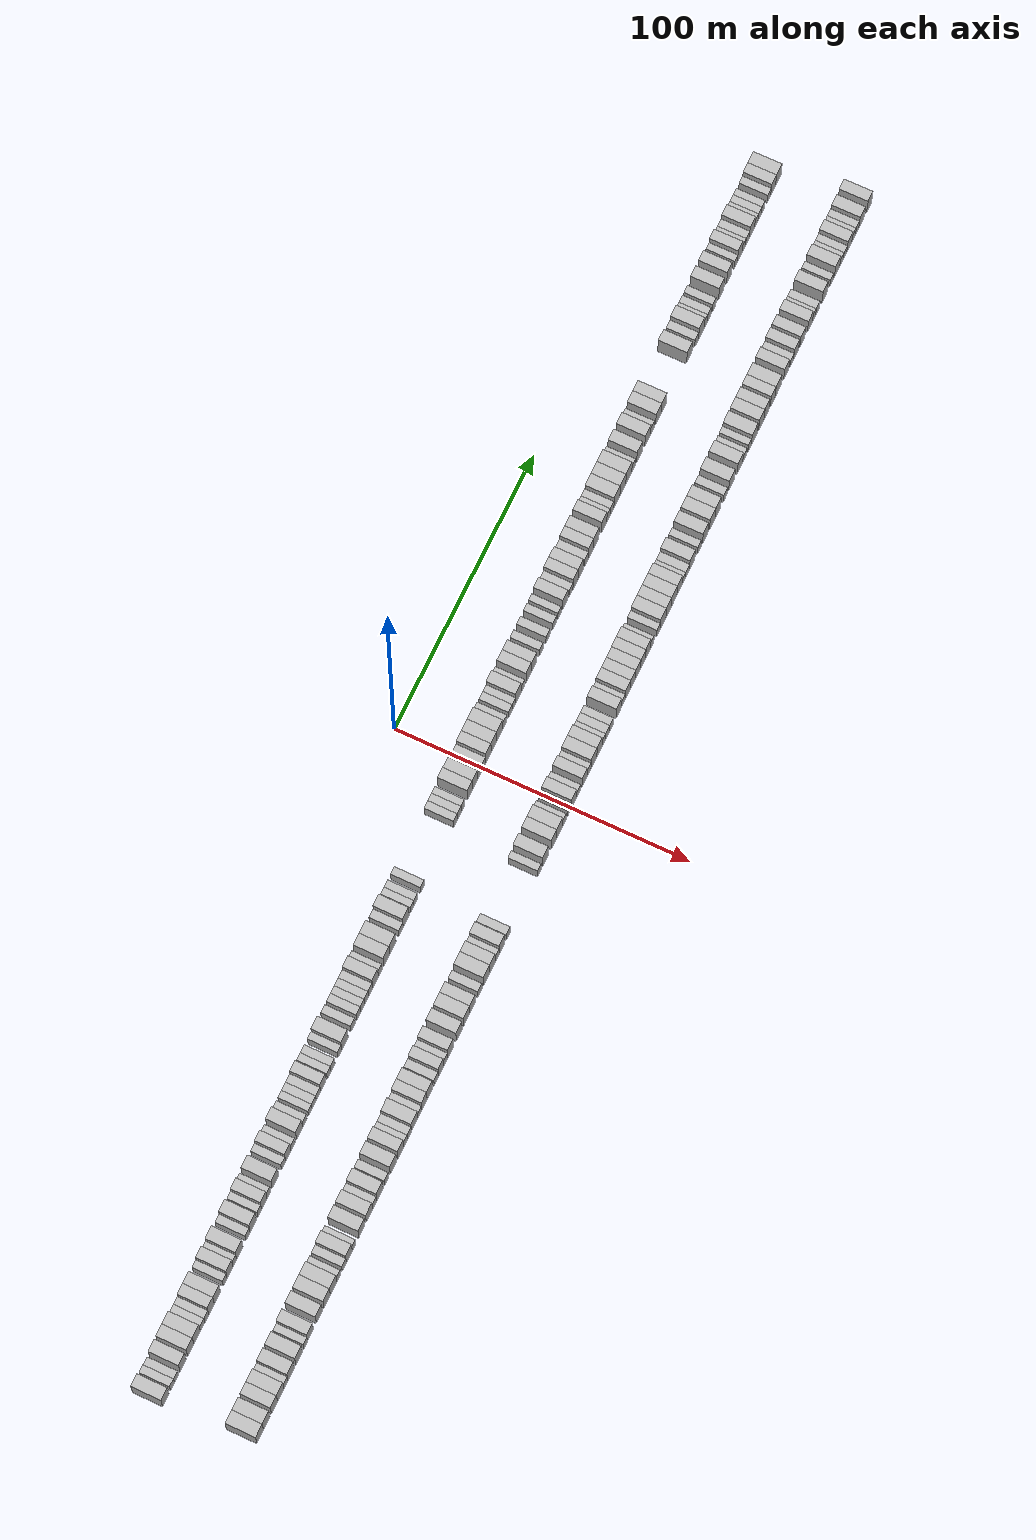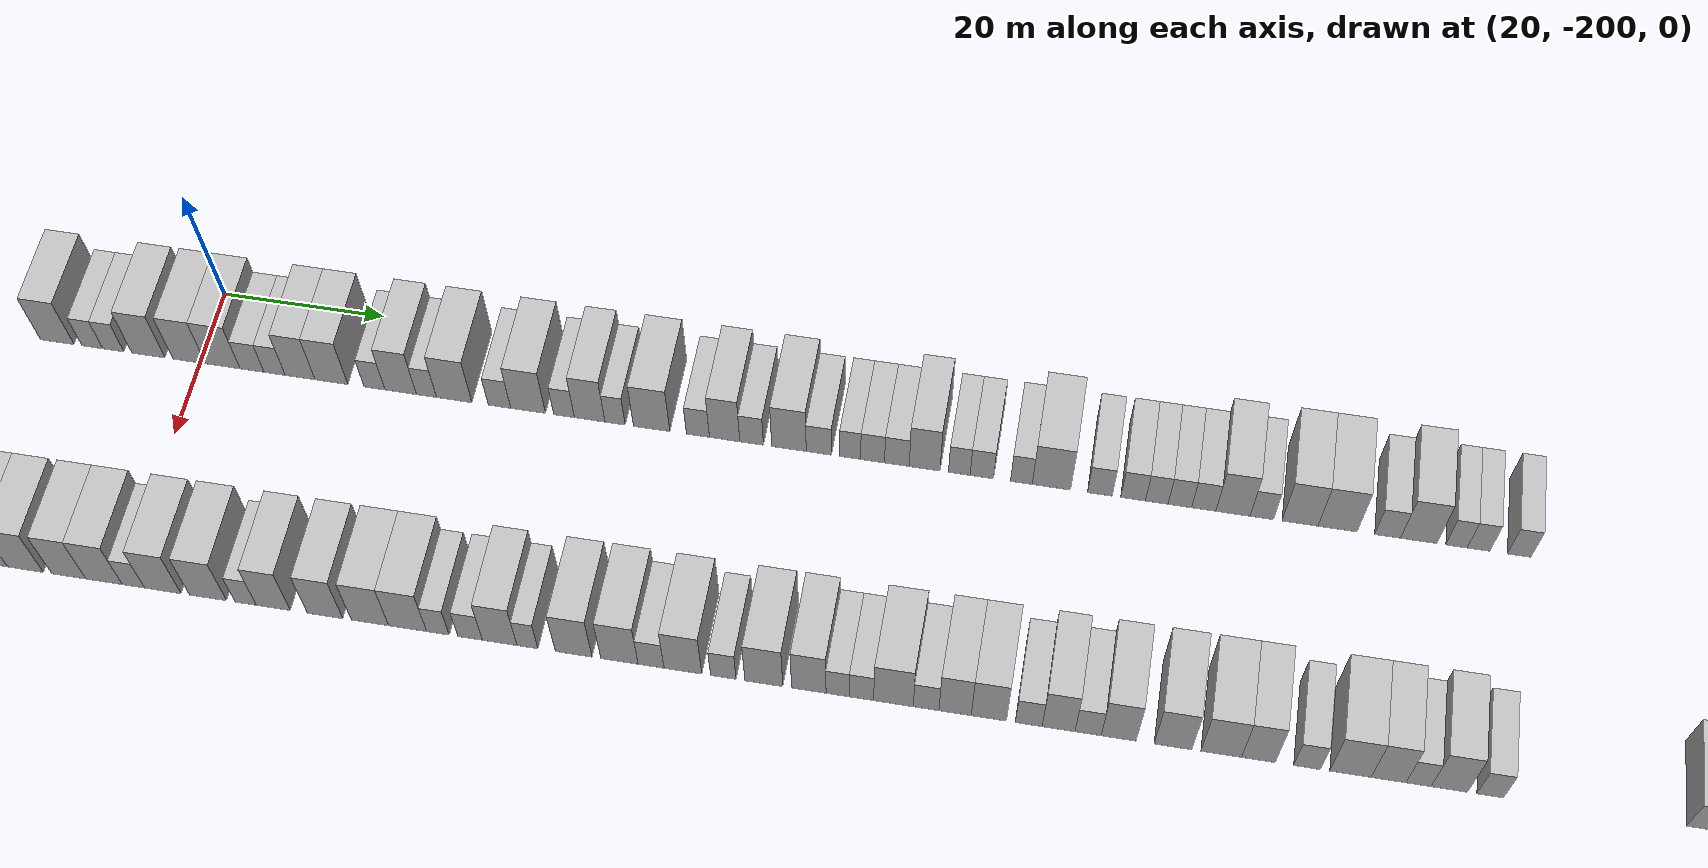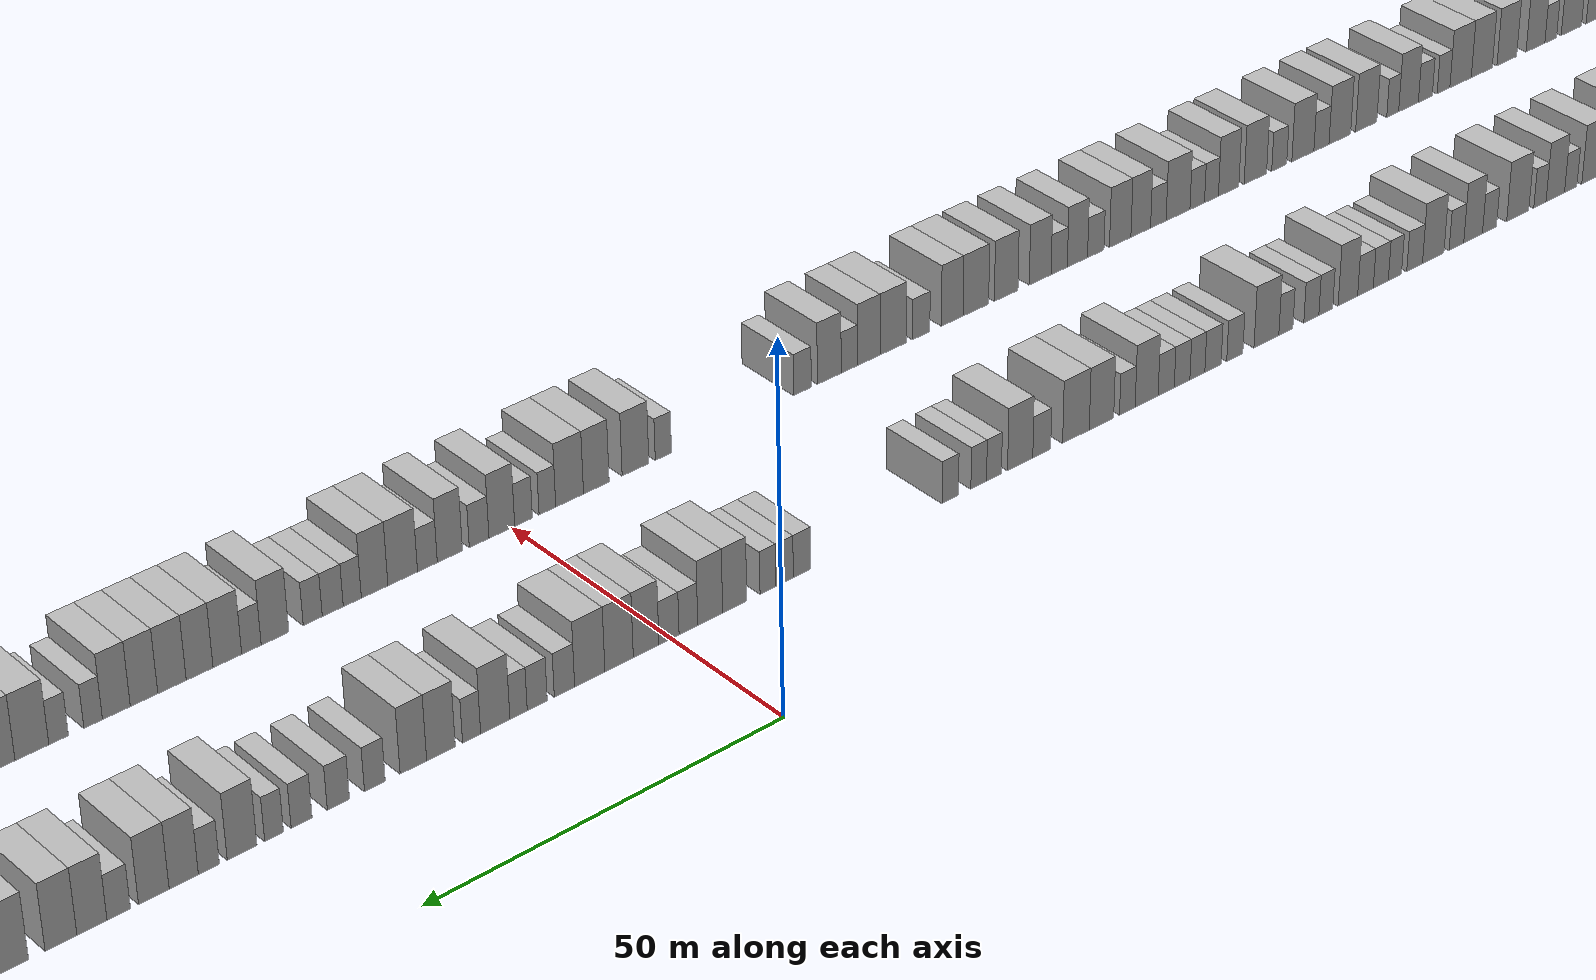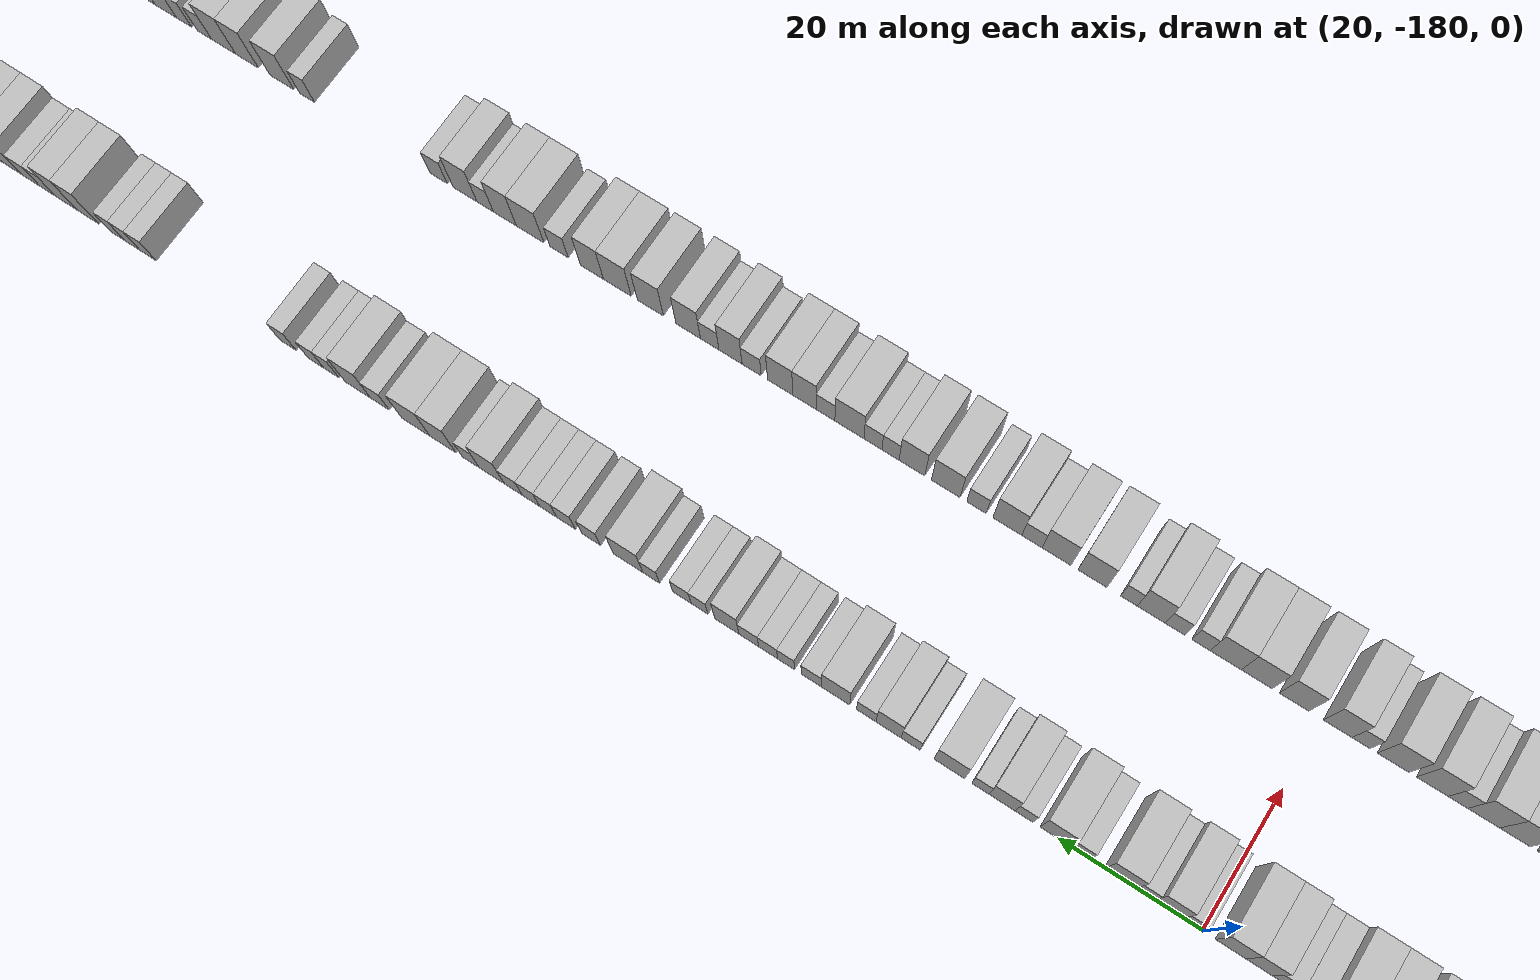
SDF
<sdf version="1.6">
 <world name="default">
  <scene>
   <sky><clouds><speed>12</speed></clouds></sky>
   <ambient>0.4 0.4 0.4 1</ambient>
   <background>0.7 0.7 0.7 1</background>
   <shadows>1</shadows>
  </scene>
  <gravity>0 0 -9.8066</gravity>
  <magnetic_field>6e-06 2.3e-05 -4.2e-05</magnetic_field>
  <physics default="0" name="default_physics" type="ode">
   <ode>
    <solver>
     <type>quick</type>
     <iters>10</iters>
     <sor>1.0</sor>
     <use_dynamic_moi_rescaling>0</use_dynamic_moi_rescaling>
    </solver>
    <constraints>
     <cfm>0</cfm>
     <erp>0.2</erp>
     <contact_max_correcting_vel>100</contact_max_correcting_vel>
     <contact_surface_layer>0.001</contact_surface_layer>
    </constraints>
   </ode>
   <max_step_size>0.004</max_step_size>
   <real_time_factor>1</real_time_factor>
   <real_time_update_rate>250</real_time_update_rate>
  </physics>
  <light name="sun" type="directional">
   <pose>0 0 10 0 0 0</pose>
   <diffuse>0.8 0.8 0.8 1</diffuse>
   <specular>0.2 0.2 0.2 1</specular>
   <attenuation>
    <range>1000</range>
    <constant>0.9</constant>
    <linear>0.01</linear>
    <quadratic>0.001</quadratic>
   </attenuation>
   <direction>-0.5 0.1 -0.9</direction>
  </light>
  <model name="building_1">
   <static>1</static>
   <pose>25.0000 -217.8961 0 0.000000 0.000000 0.000000</pose>
   <link name="link">
    <pose>0 0 4.50 0 0 0</pose>
    <collision name="collision"><geometry><box><size>10.0000 4.2077 9.0000</size></box></geometry></collision>
    <visual name="visual">
     <cast_shadows>0</cast_shadows>
     <geometry><box><size>10.0000 4.2077 9.0000</size></box></geometry>
     <material>
      <script>
       <uri>model://HANNAS_wall/materials/scripts</uri>
       <uri>model://HANNAS_wall/materials/textures</uri>
       <name>vrc/HANNAS_wall</name>
      </script>
     </material>
    </visual>
   </link>
  </model>
  <model name="building_2">
   <static>1</static>
   <pose>25.0000 -213.4765 0 0.000000 0.000000 0.000000</pose>
   <link name="link">
    <pose>0 0 3.00 0 0 0</pose>
    <collision name="collision"><geometry><box><size>10.0000 2.6316 6.0000</size></box></geometry></collision>
    <visual name="visual">
     <cast_shadows>0</cast_shadows>
     <geometry><box><size>10.0000 2.6316 6.0000</size></box></geometry>
     <material>
      <script>
       <uri>model://HANNAS_wall/materials/scripts</uri>
       <uri>model://HANNAS_wall/materials/textures</uri>
       <name>vrc/HANNAS_wall</name>
      </script>
     </material>
    </visual>
   </link>
  </model>
  <model name="building_3">
   <static>1</static>
   <pose>25.0000 -210.8408 0 0.000000 0.000000 0.000000</pose>
   <link name="link">
    <pose>0 0 3.00 0 0 0</pose>
    <collision name="collision"><geometry><box><size>10.0000 2.6396 6.0000</size></box></geometry></collision>
    <visual name="visual">
     <cast_shadows>0</cast_shadows>
     <geometry><box><size>10.0000 2.6396 6.0000</size></box></geometry>
     <material>
      <script>
       <uri>model://HANNAS_wall/materials/scripts</uri>
       <uri>model://HANNAS_wall/materials/textures</uri>
       <name>vrc/HANNAS_wall</name>
      </script>
     </material>
    </visual>
   </link>
  </model>
  <model name="building_4">
   <static>1</static>
   <pose>25.0000 -206.4568 0 0.000000 0.000000 0.000000</pose>
   <link name="link">
    <pose>0 0 4.50 0 0 0</pose>
    <collision name="collision"><geometry><box><size>10.0000 4.1285 9.0000</size></box></geometry></collision>
    <visual name="visual">
     <cast_shadows>0</cast_shadows>
     <geometry><box><size>10.0000 4.1285 9.0000</size></box></geometry>
     <material>
      <script>
       <uri>model://HANNAS_wall/materials/scripts</uri>
       <uri>model://HANNAS_wall/materials/textures</uri>
       <name>vrc/HANNAS_wall</name>
      </script>
     </material>
    </visual>
   </link>
  </model>
  <model name="building_5">
   <static>1</static>
   <pose>25.0000 -201.3536 0 0.000000 0.000000 0.000000</pose>
   <link name="link">
    <pose>0 0 4.50 0 0 0</pose>
    <collision name="collision"><geometry><box><size>10.0000 4.0779 9.0000</size></box></geometry></collision>
    <visual name="visual">
     <cast_shadows>0</cast_shadows>
     <geometry><box><size>10.0000 4.0779 9.0000</size></box></geometry>
     <material>
      <script>
       <uri>model://HANNAS_wall/materials/scripts</uri>
       <uri>model://HANNAS_wall/materials/textures</uri>
       <name>vrc/HANNAS_wall</name>
      </script>
     </material>
    </visual>
   </link>
  </model>
  <model name="building_6">
   <static>1</static>
   <pose>25.0000 -197.1710 0 0.000000 0.000000 0.000000</pose>
   <link name="link">
    <pose>0 0 4.50 0 0 0</pose>
    <collision name="collision"><geometry><box><size>10.0000 4.2873 9.0000</size></box></geometry></collision>
    <visual name="visual">
     <cast_shadows>0</cast_shadows>
     <geometry><box><size>10.0000 4.2873 9.0000</size></box></geometry>
     <material>
      <script>
       <uri>model://HANNAS_wall/materials/scripts</uri>
       <uri>model://HANNAS_wall/materials/textures</uri>
       <name>vrc/HANNAS_wall</name>
      </script>
     </material>
    </visual>
   </link>
  </model>
  <model name="building_7">
   <static>1</static>
   <pose>25.0000 -193.5384 0 0.000000 0.000000 0.000000</pose>
   <link name="link">
    <pose>0 0 3.00 0 0 0</pose>
    <collision name="collision"><geometry><box><size>10.0000 2.9780 6.0000</size></box></geometry></collision>
    <visual name="visual">
     <cast_shadows>0</cast_shadows>
     <geometry><box><size>10.0000 2.9780 6.0000</size></box></geometry>
     <material>
      <script>
       <uri>model://HANNAS_wall/materials/scripts</uri>
       <uri>model://HANNAS_wall/materials/textures</uri>
       <name>vrc/HANNAS_wall</name>
      </script>
     </material>
    </visual>
   </link>
  </model>
  <model name="building_8">
   <static>1</static>
   <pose>25.0000 -190.7405 0 0.000000 0.000000 0.000000</pose>
   <link name="link">
    <pose>0 0 3.00 0 0 0</pose>
    <collision name="collision"><geometry><box><size>10.0000 2.6176 6.0000</size></box></geometry></collision>
    <visual name="visual">
     <cast_shadows>0</cast_shadows>
     <geometry><box><size>10.0000 2.6176 6.0000</size></box></geometry>
     <material>
      <script>
       <uri>model://HANNAS_wall/materials/scripts</uri>
       <uri>model://HANNAS_wall/materials/textures</uri>
       <name>vrc/HANNAS_wall</name>
      </script>
     </material>
    </visual>
   </link>
  </model>
  <model name="building_9">
   <static>1</static>
   <pose>25.0000 -187.5881 0 0.000000 0.000000 0.000000</pose>
   <link name="link">
    <pose>0 0 4.50 0 0 0</pose>
    <collision name="collision"><geometry><box><size>10.0000 3.6871 9.0000</size></box></geometry></collision>
    <visual name="visual">
     <cast_shadows>0</cast_shadows>
     <geometry><box><size>10.0000 3.6871 9.0000</size></box></geometry>
     <material>
      <script>
       <uri>model://HANNAS_wall/materials/scripts</uri>
       <uri>model://HANNAS_wall/materials/textures</uri>
       <name>vrc/HANNAS_wall</name>
      </script>
     </material>
    </visual>
   </link>
  </model>
  <model name="building_10">
   <static>1</static>
   <pose>25.0000 -183.7218 0 0.000000 0.000000 0.000000</pose>
   <link name="link">
    <pose>0 0 4.50 0 0 0</pose>
    <collision name="collision"><geometry><box><size>10.0000 4.0456 9.0000</size></box></geometry></collision>
    <visual name="visual">
     <cast_shadows>0</cast_shadows>
     <geometry><box><size>10.0000 4.0456 9.0000</size></box></geometry>
     <material>
      <script>
       <uri>model://HANNAS_wall/materials/scripts</uri>
       <uri>model://HANNAS_wall/materials/textures</uri>
       <name>vrc/HANNAS_wall</name>
      </script>
     </material>
    </visual>
   </link>
  </model>
  <model name="building_11">
   <static>1</static>
   <pose>25.0000 -178.4140 0 0.000000 0.000000 0.000000</pose>
   <link name="link">
    <pose>0 0 3.00 0 0 0</pose>
    <collision name="collision"><geometry><box><size>10.0000 2.5701 6.0000</size></box></geometry></collision>
    <visual name="visual">
     <cast_shadows>0</cast_shadows>
     <geometry><box><size>10.0000 2.5701 6.0000</size></box></geometry>
     <material>
      <script>
       <uri>model://HANNAS_wall/materials/scripts</uri>
       <uri>model://HANNAS_wall/materials/textures</uri>
       <name>vrc/HANNAS_wall</name>
      </script>
     </material>
    </visual>
   </link>
  </model>
  <model name="building_12">
   <static>1</static>
   <pose>25.0000 -175.1994 0 0.000000 0.000000 0.000000</pose>
   <link name="link">
    <pose>0 0 4.50 0 0 0</pose>
    <collision name="collision"><geometry><box><size>10.0000 3.8590 9.0000</size></box></geometry></collision>
    <visual name="visual">
     <cast_shadows>0</cast_shadows>
     <geometry><box><size>10.0000 3.8590 9.0000</size></box></geometry>
     <material>
      <script>
       <uri>model://HANNAS_wall/materials/scripts</uri>
       <uri>model://HANNAS_wall/materials/textures</uri>
       <name>vrc/HANNAS_wall</name>
      </script>
     </material>
    </visual>
   </link>
  </model>
  <model name="building_13">
   <static>1</static>
   <pose>25.0000 -172.0381 0 0.000000 0.000000 0.000000</pose>
   <link name="link">
    <pose>0 0 3.00 0 0 0</pose>
    <collision name="collision"><geometry><box><size>10.0000 2.4635 6.0000</size></box></geometry></collision>
    <visual name="visual">
     <cast_shadows>0</cast_shadows>
     <geometry><box><size>10.0000 2.4635 6.0000</size></box></geometry>
     <material>
      <script>
       <uri>model://HANNAS_wall/materials/scripts</uri>
       <uri>model://HANNAS_wall/materials/textures</uri>
       <name>vrc/HANNAS_wall</name>
      </script>
     </material>
    </visual>
   </link>
  </model>
  <model name="building_14">
   <static>1</static>
   <pose>25.0000 -168.6430 0 0.000000 0.000000 0.000000</pose>
   <link name="link">
    <pose>0 0 4.50 0 0 0</pose>
    <collision name="collision"><geometry><box><size>10.0000 4.3266 9.0000</size></box></geometry></collision>
    <visual name="visual">
     <cast_shadows>0</cast_shadows>
     <geometry><box><size>10.0000 4.3266 9.0000</size></box></geometry>
     <material>
      <script>
       <uri>model://HANNAS_wall/materials/scripts</uri>
       <uri>model://HANNAS_wall/materials/textures</uri>
       <name>vrc/HANNAS_wall</name>
      </script>
     </material>
    </visual>
   </link>
  </model>
  <model name="building_15">
   <static>1</static>
   <pose>25.0000 -163.1092 0 0.000000 0.000000 0.000000</pose>
   <link name="link">
    <pose>0 0 3.00 0 0 0</pose>
    <collision name="collision"><geometry><box><size>10.0000 2.7412 6.0000</size></box></geometry></collision>
    <visual name="visual">
     <cast_shadows>0</cast_shadows>
     <geometry><box><size>10.0000 2.7412 6.0000</size></box></geometry>
     <material>
      <script>
       <uri>model://HANNAS_wall/materials/scripts</uri>
       <uri>model://HANNAS_wall/materials/textures</uri>
       <name>vrc/HANNAS_wall</name>
      </script>
     </material>
    </visual>
   </link>
  </model>
  <model name="building_16">
   <static>1</static>
   <pose>25.0000 -159.6226 0 0.000000 0.000000 0.000000</pose>
   <link name="link">
    <pose>0 0 4.50 0 0 0</pose>
    <collision name="collision"><geometry><box><size>10.0000 4.2318 9.0000</size></box></geometry></collision>
    <visual name="visual">
     <cast_shadows>0</cast_shadows>
     <geometry><box><size>10.0000 4.2318 9.0000</size></box></geometry>
     <material>
      <script>
       <uri>model://HANNAS_wall/materials/scripts</uri>
       <uri>model://HANNAS_wall/materials/textures</uri>
       <name>vrc/HANNAS_wall</name>
      </script>
     </material>
    </visual>
   </link>
  </model>
  <model name="building_17">
   <static>1</static>
   <pose>25.0000 -155.2536 0 0.000000 0.000000 0.000000</pose>
   <link name="link">
    <pose>0 0 3.00 0 0 0</pose>
    <collision name="collision"><geometry><box><size>10.0000 2.5063 6.0000</size></box></geometry></collision>
    <visual name="visual">
     <cast_shadows>0</cast_shadows>
     <geometry><box><size>10.0000 2.5063 6.0000</size></box></geometry>
     <material>
      <script>
       <uri>model://HANNAS_wall/materials/scripts</uri>
       <uri>model://HANNAS_wall/materials/textures</uri>
       <name>vrc/HANNAS_wall</name>
      </script>
     </material>
    </visual>
   </link>
  </model>
  <model name="building_18">
   <static>1</static>
   <pose>25.0000 -152.1477 0 0.000000 0.000000 0.000000</pose>
   <link name="link">
    <pose>0 0 4.50 0 0 0</pose>
    <collision name="collision"><geometry><box><size>10.0000 3.7055 9.0000</size></box></geometry></collision>
    <visual name="visual">
     <cast_shadows>0</cast_shadows>
     <geometry><box><size>10.0000 3.7055 9.0000</size></box></geometry>
     <material>
      <script>
       <uri>model://HANNAS_wall/materials/scripts</uri>
       <uri>model://HANNAS_wall/materials/textures</uri>
       <name>vrc/HANNAS_wall</name>
      </script>
     </material>
    </visual>
   </link>
  </model>
  <model name="building_19">
   <static>1</static>
   <pose>25.0000 -149.0705 0 0.000000 0.000000 0.000000</pose>
   <link name="link">
    <pose>0 0 3.00 0 0 0</pose>
    <collision name="collision"><geometry><box><size>10.0000 2.4488 6.0000</size></box></geometry></collision>
    <visual name="visual">
     <cast_shadows>0</cast_shadows>
     <geometry><box><size>10.0000 2.4488 6.0000</size></box></geometry>
     <material>
      <script>
       <uri>model://HANNAS_wall/materials/scripts</uri>
       <uri>model://HANNAS_wall/materials/textures</uri>
       <name>vrc/HANNAS_wall</name>
      </script>
     </material>
    </visual>
   </link>
  </model>
  <model name="building_20">
   <static>1</static>
   <pose>25.0000 -144.6544 0 0.000000 0.000000 0.000000</pose>
   <link name="link">
    <pose>0 0 4.50 0 0 0</pose>
    <collision name="collision"><geometry><box><size>10.0000 4.3834 9.0000</size></box></geometry></collision>
    <visual name="visual">
     <cast_shadows>0</cast_shadows>
     <geometry><box><size>10.0000 4.3834 9.0000</size></box></geometry>
     <material>
      <script>
       <uri>model://HANNAS_wall/materials/scripts</uri>
       <uri>model://HANNAS_wall/materials/textures</uri>
       <name>vrc/HANNAS_wall</name>
      </script>
     </material>
    </visual>
   </link>
  </model>
  <model name="building_21">
   <static>1</static>
   <pose>25.0000 -139.0857 0 0.000000 0.000000 0.000000</pose>
   <link name="link">
    <pose>0 0 3.00 0 0 0</pose>
    <collision name="collision"><geometry><box><size>10.0000 2.7540 6.0000</size></box></geometry></collision>
    <visual name="visual">
     <cast_shadows>0</cast_shadows>
     <geometry><box><size>10.0000 2.7540 6.0000</size></box></geometry>
     <material>
      <script>
       <uri>model://HANNAS_wall/materials/scripts</uri>
       <uri>model://HANNAS_wall/materials/textures</uri>
       <name>vrc/HANNAS_wall</name>
      </script>
     </material>
    </visual>
   </link>
  </model>
  <model name="building_22">
   <static>1</static>
   <pose>25.0000 -135.8844 0 0.000000 0.000000 0.000000</pose>
   <link name="link">
    <pose>0 0 4.50 0 0 0</pose>
    <collision name="collision"><geometry><box><size>10.0000 3.6485 9.0000</size></box></geometry></collision>
    <visual name="visual">
     <cast_shadows>0</cast_shadows>
     <geometry><box><size>10.0000 3.6485 9.0000</size></box></geometry>
     <material>
      <script>
       <uri>model://HANNAS_wall/materials/scripts</uri>
       <uri>model://HANNAS_wall/materials/textures</uri>
       <name>vrc/HANNAS_wall</name>
      </script>
     </material>
    </visual>
   </link>
  </model>
  <model name="building_23">
   <static>1</static>
   <pose>25.0000 -132.6452 0 0.000000 0.000000 0.000000</pose>
   <link name="link">
    <pose>0 0 3.00 0 0 0</pose>
    <collision name="collision"><geometry><box><size>10.0000 2.8299 6.0000</size></box></geometry></collision>
    <visual name="visual">
     <cast_shadows>0</cast_shadows>
     <geometry><box><size>10.0000 2.8299 6.0000</size></box></geometry>
     <material>
      <script>
       <uri>model://HANNAS_wall/materials/scripts</uri>
       <uri>model://HANNAS_wall/materials/textures</uri>
       <name>vrc/HANNAS_wall</name>
      </script>
     </material>
    </visual>
   </link>
  </model>
  <model name="building_24">
   <static>1</static>
   <pose>25.0000 -128.1706 0 0.000000 0.000000 0.000000</pose>
   <link name="link">
    <pose>0 0 4.50 0 0 0</pose>
    <collision name="collision"><geometry><box><size>10.0000 4.1194 9.0000</size></box></geometry></collision>
    <visual name="visual">
     <cast_shadows>0</cast_shadows>
     <geometry><box><size>10.0000 4.1194 9.0000</size></box></geometry>
     <material>
      <script>
       <uri>model://HANNAS_wall/materials/scripts</uri>
       <uri>model://HANNAS_wall/materials/textures</uri>
       <name>vrc/HANNAS_wall</name>
      </script>
     </material>
    </visual>
   </link>
  </model>
  <model name="building_25">
   <static>1</static>
   <pose>25.0000 -124.6140 0 0.000000 0.000000 0.000000</pose>
   <link name="link">
    <pose>0 0 3.00 0 0 0</pose>
    <collision name="collision"><geometry><box><size>10.0000 2.9939 6.0000</size></box></geometry></collision>
    <visual name="visual">
     <cast_shadows>0</cast_shadows>
     <geometry><box><size>10.0000 2.9939 6.0000</size></box></geometry>
     <material>
      <script>
       <uri>model://HANNAS_wall/materials/scripts</uri>
       <uri>model://HANNAS_wall/materials/textures</uri>
       <name>vrc/HANNAS_wall</name>
      </script>
     </material>
    </visual>
   </link>
  </model>
  <model name="building_26">
   <static>1</static>
   <pose>25.0000 -120.8697 0 0.000000 0.000000 0.000000</pose>
   <link name="link">
    <pose>0 0 3.00 0 0 0</pose>
    <collision name="collision"><geometry><box><size>10.0000 2.4948 6.0000</size></box></geometry></collision>
    <visual name="visual">
     <cast_shadows>0</cast_shadows>
     <geometry><box><size>10.0000 2.4948 6.0000</size></box></geometry>
     <material>
      <script>
       <uri>model://HANNAS_wall/materials/scripts</uri>
       <uri>model://HANNAS_wall/materials/textures</uri>
       <name>vrc/HANNAS_wall</name>
      </script>
     </material>
    </visual>
   </link>
  </model>
  <model name="building_27">
   <static>1</static>
   <pose>25.0000 -118.2075 0 0.000000 0.000000 0.000000</pose>
   <link name="link">
    <pose>0 0 3.00 0 0 0</pose>
    <collision name="collision"><geometry><box><size>10.0000 2.8295 6.0000</size></box></geometry></collision>
    <visual name="visual">
     <cast_shadows>0</cast_shadows>
     <geometry><box><size>10.0000 2.8295 6.0000</size></box></geometry>
     <material>
      <script>
       <uri>model://HANNAS_wall/materials/scripts</uri>
       <uri>model://HANNAS_wall/materials/textures</uri>
       <name>vrc/HANNAS_wall</name>
      </script>
     </material>
    </visual>
   </link>
  </model>
  <model name="building_28">
   <static>1</static>
   <pose>25.0000 -115.3302 0 0.000000 0.000000 0.000000</pose>
   <link name="link">
    <pose>0 0 3.00 0 0 0</pose>
    <collision name="collision"><geometry><box><size>10.0000 2.9252 6.0000</size></box></geometry></collision>
    <visual name="visual">
     <cast_shadows>0</cast_shadows>
     <geometry><box><size>10.0000 2.9252 6.0000</size></box></geometry>
     <material>
      <script>
       <uri>model://HANNAS_wall/materials/scripts</uri>
       <uri>model://HANNAS_wall/materials/textures</uri>
       <name>vrc/HANNAS_wall</name>
      </script>
     </material>
    </visual>
   </link>
  </model>
  <model name="building_29">
   <static>1</static>
   <pose>25.0000 -112.0483 0 0.000000 0.000000 0.000000</pose>
   <link name="link">
    <pose>0 0 4.50 0 0 0</pose>
    <collision name="collision"><geometry><box><size>10.0000 3.6387 9.0000</size></box></geometry></collision>
    <visual name="visual">
     <cast_shadows>0</cast_shadows>
     <geometry><box><size>10.0000 3.6387 9.0000</size></box></geometry>
     <material>
      <script>
       <uri>model://HANNAS_wall/materials/scripts</uri>
       <uri>model://HANNAS_wall/materials/textures</uri>
       <name>vrc/HANNAS_wall</name>
      </script>
     </material>
    </visual>
   </link>
  </model>
  <model name="building_30">
   <static>1</static>
   <pose>25.0000 -107.9524 0 0.000000 0.000000 0.000000</pose>
   <link name="link">
    <pose>0 0 3.00 0 0 0</pose>
    <collision name="collision"><geometry><box><size>10.0000 2.5531 6.0000</size></box></geometry></collision>
    <visual name="visual">
     <cast_shadows>0</cast_shadows>
     <geometry><box><size>10.0000 2.5531 6.0000</size></box></geometry>
     <material>
      <script>
       <uri>model://HANNAS_wall/materials/scripts</uri>
       <uri>model://HANNAS_wall/materials/textures</uri>
       <name>vrc/HANNAS_wall</name>
      </script>
     </material>
    </visual>
   </link>
  </model>
  <model name="building_31">
   <static>1</static>
   <pose>25.0000 -105.2951 0 0.000000 0.000000 0.000000</pose>
   <link name="link">
    <pose>0 0 3.00 0 0 0</pose>
    <collision name="collision"><geometry><box><size>10.0000 2.7616 6.0000</size></box></geometry></collision>
    <visual name="visual">
     <cast_shadows>0</cast_shadows>
     <geometry><box><size>10.0000 2.7616 6.0000</size></box></geometry>
     <material>
      <script>
       <uri>model://HANNAS_wall/materials/scripts</uri>
       <uri>model://HANNAS_wall/materials/textures</uri>
       <name>vrc/HANNAS_wall</name>
      </script>
     </material>
    </visual>
   </link>
  </model>
  <model name="building_32">
   <static>1</static>
   <pose>25.0000 -100.6387 0 0.000000 0.000000 0.000000</pose>
   <link name="link">
    <pose>0 0 3.00 0 0 0</pose>
    <collision name="collision"><geometry><box><size>10.0000 2.5512 6.0000</size></box></geometry></collision>
    <visual name="visual">
     <cast_shadows>0</cast_shadows>
     <geometry><box><size>10.0000 2.5512 6.0000</size></box></geometry>
     <material>
      <script>
       <uri>model://HANNAS_wall/materials/scripts</uri>
       <uri>model://HANNAS_wall/materials/textures</uri>
       <name>vrc/HANNAS_wall</name>
      </script>
     </material>
    </visual>
   </link>
  </model>
  <model name="building_33">
   <static>1</static>
   <pose>25.0000 -97.1202 0 0.000000 0.000000 0.000000</pose>
   <link name="link">
    <pose>0 0 4.50 0 0 0</pose>
    <collision name="collision"><geometry><box><size>10.0000 4.4859 9.0000</size></box></geometry></collision>
    <visual name="visual">
     <cast_shadows>0</cast_shadows>
     <geometry><box><size>10.0000 4.4859 9.0000</size></box></geometry>
     <material>
      <script>
       <uri>model://HANNAS_wall/materials/scripts</uri>
       <uri>model://HANNAS_wall/materials/textures</uri>
       <name>vrc/HANNAS_wall</name>
      </script>
     </material>
    </visual>
   </link>
  </model>
  <model name="building_34">
   <static>1</static>
   <pose>25.0000 -91.4391 0 0.000000 0.000000 0.000000</pose>
   <link name="link">
    <pose>0 0 3.00 0 0 0</pose>
    <collision name="collision"><geometry><box><size>10.0000 2.8762 6.0000</size></box></geometry></collision>
    <visual name="visual">
     <cast_shadows>0</cast_shadows>
     <geometry><box><size>10.0000 2.8762 6.0000</size></box></geometry>
     <material>
      <script>
       <uri>model://HANNAS_wall/materials/scripts</uri>
       <uri>model://HANNAS_wall/materials/textures</uri>
       <name>vrc/HANNAS_wall</name>
      </script>
     </material>
    </visual>
   </link>
  </model>
  <model name="building_35">
   <static>1</static>
   <pose>25.0000 -87.5607 0 0.000000 0.000000 0.000000</pose>
   <link name="link">
    <pose>0 0 3.00 0 0 0</pose>
    <collision name="collision"><geometry><box><size>10.0000 2.8806 6.0000</size></box></geometry></collision>
    <visual name="visual">
     <cast_shadows>0</cast_shadows>
     <geometry><box><size>10.0000 2.8806 6.0000</size></box></geometry>
     <material>
      <script>
       <uri>model://HANNAS_wall/materials/scripts</uri>
       <uri>model://HANNAS_wall/materials/textures</uri>
       <name>vrc/HANNAS_wall</name>
      </script>
     </material>
    </visual>
   </link>
  </model>
  <model name="building_36">
   <static>1</static>
   <pose>25.0000 -84.8010 0 0.000000 0.000000 0.000000</pose>
   <link name="link">
    <pose>0 0 3.00 0 0 0</pose>
    <collision name="collision"><geometry><box><size>10.0000 2.6389 6.0000</size></box></geometry></collision>
    <visual name="visual">
     <cast_shadows>0</cast_shadows>
     <geometry><box><size>10.0000 2.6389 6.0000</size></box></geometry>
     <material>
      <script>
       <uri>model://HANNAS_wall/materials/scripts</uri>
       <uri>model://HANNAS_wall/materials/textures</uri>
       <name>vrc/HANNAS_wall</name>
      </script>
     </material>
    </visual>
   </link>
  </model>
  <model name="building_37">
   <static>1</static>
   <pose>25.0000 -82.1137 0 0.000000 0.000000 0.000000</pose>
   <link name="link">
    <pose>0 0 3.00 0 0 0</pose>
    <collision name="collision"><geometry><box><size>10.0000 2.7355 6.0000</size></box></geometry></collision>
    <visual name="visual">
     <cast_shadows>0</cast_shadows>
     <geometry><box><size>10.0000 2.7355 6.0000</size></box></geometry>
     <material>
      <script>
       <uri>model://HANNAS_wall/materials/scripts</uri>
       <uri>model://HANNAS_wall/materials/textures</uri>
       <name>vrc/HANNAS_wall</name>
      </script>
     </material>
    </visual>
   </link>
  </model>
  <model name="building_38">
   <static>1</static>
   <pose>25.0000 -79.3378 0 0.000000 0.000000 0.000000</pose>
   <link name="link">
    <pose>0 0 3.00 0 0 0</pose>
    <collision name="collision"><geometry><box><size>10.0000 2.8163 6.0000</size></box></geometry></collision>
    <visual name="visual">
     <cast_shadows>0</cast_shadows>
     <geometry><box><size>10.0000 2.8163 6.0000</size></box></geometry>
     <material>
      <script>
       <uri>model://HANNAS_wall/materials/scripts</uri>
       <uri>model://HANNAS_wall/materials/textures</uri>
       <name>vrc/HANNAS_wall</name>
      </script>
     </material>
    </visual>
   </link>
  </model>
  <model name="building_39">
   <static>1</static>
   <pose>25.0000 -75.9396 0 0.000000 0.000000 0.000000</pose>
   <link name="link">
    <pose>0 0 4.50 0 0 0</pose>
    <collision name="collision"><geometry><box><size>10.0000 3.9802 9.0000</size></box></geometry></collision>
    <visual name="visual">
     <cast_shadows>0</cast_shadows>
     <geometry><box><size>10.0000 3.9802 9.0000</size></box></geometry>
     <material>
      <script>
       <uri>model://HANNAS_wall/materials/scripts</uri>
       <uri>model://HANNAS_wall/materials/textures</uri>
       <name>vrc/HANNAS_wall</name>
      </script>
     </material>
    </visual>
   </link>
  </model>
  <model name="building_40">
   <static>1</static>
   <pose>25.0000 -72.6092 0 0.000000 0.000000 0.000000</pose>
   <link name="link">
    <pose>0 0 3.00 0 0 0</pose>
    <collision name="collision"><geometry><box><size>10.0000 2.6807 6.0000</size></box></geometry></collision>
    <visual name="visual">
     <cast_shadows>0</cast_shadows>
     <geometry><box><size>10.0000 2.6807 6.0000</size></box></geometry>
     <material>
      <script>
       <uri>model://HANNAS_wall/materials/scripts</uri>
       <uri>model://HANNAS_wall/materials/textures</uri>
       <name>vrc/HANNAS_wall</name>
      </script>
     </material>
    </visual>
   </link>
  </model>
  <model name="building_41">
   <static>1</static>
   <pose>25.0000 -68.1912 0 0.000000 0.000000 0.000000</pose>
   <link name="link">
    <pose>0 0 4.50 0 0 0</pose>
    <collision name="collision"><geometry><box><size>10.0000 4.1552 9.0000</size></box></geometry></collision>
    <visual name="visual">
     <cast_shadows>0</cast_shadows>
     <geometry><box><size>10.0000 4.1552 9.0000</size></box></geometry>
     <material>
      <script>
       <uri>model://HANNAS_wall/materials/scripts</uri>
       <uri>model://HANNAS_wall/materials/textures</uri>
       <name>vrc/HANNAS_wall</name>
      </script>
     </material>
    </visual>
   </link>
  </model>
  <model name="building_42">
   <static>1</static>
   <pose>25.0000 -63.8648 0 0.000000 0.000000 0.000000</pose>
   <link name="link">
    <pose>0 0 4.50 0 0 0</pose>
    <collision name="collision"><geometry><box><size>10.0000 4.4976 9.0000</size></box></geometry></collision>
    <visual name="visual">
     <cast_shadows>0</cast_shadows>
     <geometry><box><size>10.0000 4.4976 9.0000</size></box></geometry>
     <material>
      <script>
       <uri>model://HANNAS_wall/materials/scripts</uri>
       <uri>model://HANNAS_wall/materials/textures</uri>
       <name>vrc/HANNAS_wall</name>
      </script>
     </material>
    </visual>
   </link>
  </model>
  <model name="building_43">
   <static>1</static>
   <pose>25.0000 -58.1235 0 0.000000 0.000000 0.000000</pose>
   <link name="link">
    <pose>0 0 3.00 0 0 0</pose>
    <collision name="collision"><geometry><box><size>10.0000 2.9851 6.0000</size></box></geometry></collision>
    <visual name="visual">
     <cast_shadows>0</cast_shadows>
     <geometry><box><size>10.0000 2.9851 6.0000</size></box></geometry>
     <material>
      <script>
       <uri>model://HANNAS_wall/materials/scripts</uri>
       <uri>model://HANNAS_wall/materials/textures</uri>
       <name>vrc/HANNAS_wall</name>
      </script>
     </material>
    </visual>
   </link>
  </model>
  <model name="building_44">
   <static>1</static>
   <pose>25.0000 -54.5474 0 0.000000 0.000000 0.000000</pose>
   <link name="link">
    <pose>0 0 4.50 0 0 0</pose>
    <collision name="collision"><geometry><box><size>10.0000 4.1671 9.0000</size></box></geometry></collision>
    <visual name="visual">
     <cast_shadows>0</cast_shadows>
     <geometry><box><size>10.0000 4.1671 9.0000</size></box></geometry>
     <material>
      <script>
       <uri>model://HANNAS_wall/materials/scripts</uri>
       <uri>model://HANNAS_wall/materials/textures</uri>
       <name>vrc/HANNAS_wall</name>
      </script>
     </material>
    </visual>
   </link>
  </model>
  <model name="building_45">
   <static>1</static>
   <pose>25.0000 -50.2409 0 0.000000 0.000000 0.000000</pose>
   <link name="link">
    <pose>0 0 3.00 0 0 0</pose>
    <collision name="collision"><geometry><box><size>10.0000 2.4461 6.0000</size></box></geometry></collision>
    <visual name="visual">
     <cast_shadows>0</cast_shadows>
     <geometry><box><size>10.0000 2.4461 6.0000</size></box></geometry>
     <material>
      <script>
       <uri>model://HANNAS_wall/materials/scripts</uri>
       <uri>model://HANNAS_wall/materials/textures</uri>
       <name>vrc/HANNAS_wall</name>
      </script>
     </material>
    </visual>
   </link>
  </model>
  <model name="building_46">
   <static>1</static>
   <pose>25.0000 -47.7327 0 0.000000 0.000000 0.000000</pose>
   <link name="link">
    <pose>0 0 3.00 0 0 0</pose>
    <collision name="collision"><geometry><box><size>10.0000 2.5703 6.0000</size></box></geometry></collision>
    <visual name="visual">
     <cast_shadows>0</cast_shadows>
     <geometry><box><size>10.0000 2.5703 6.0000</size></box></geometry>
     <material>
      <script>
       <uri>model://HANNAS_wall/materials/scripts</uri>
       <uri>model://HANNAS_wall/materials/textures</uri>
       <name>vrc/HANNAS_wall</name>
      </script>
     </material>
    </visual>
   </link>
  </model>
  <model name="building_47">
   <static>1</static>
   <pose>25.0000 -43.1132 0 0.000000 0.000000 0.000000</pose>
   <link name="link">
    <pose>0 0 3.00 0 0 0</pose>
    <collision name="collision"><geometry><box><size>10.0000 2.6686 6.0000</size></box></geometry></collision>
    <visual name="visual">
     <cast_shadows>0</cast_shadows>
     <geometry><box><size>10.0000 2.6686 6.0000</size></box></geometry>
     <material>
      <script>
       <uri>model://HANNAS_wall/materials/scripts</uri>
       <uri>model://HANNAS_wall/materials/textures</uri>
       <name>vrc/HANNAS_wall</name>
      </script>
     </material>
    </visual>
   </link>
  </model>
  <model name="building_48">
   <static>1</static>
   <pose>25.0000 -19.7409 0 0.000000 0.000000 0.000000</pose>
   <link name="link">
    <pose>0 0 3.00 0 0 0</pose>
    <collision name="collision"><geometry><box><size>10.0000 2.6920 6.0000</size></box></geometry></collision>
    <visual name="visual">
     <cast_shadows>0</cast_shadows>
     <geometry><box><size>10.0000 2.6920 6.0000</size></box></geometry>
     <material>
      <script>
       <uri>model://HANNAS_wall/materials/scripts</uri>
       <uri>model://HANNAS_wall/materials/textures</uri>
       <name>vrc/HANNAS_wall</name>
      </script>
     </material>
    </visual>
   </link>
  </model>
  <model name="building_49">
   <static>1</static>
   <pose>25.0000 -17.0613 0 0.000000 0.000000 0.000000</pose>
   <link name="link">
    <pose>0 0 3.00 0 0 0</pose>
    <collision name="collision"><geometry><box><size>10.0000 2.6673 6.0000</size></box></geometry></collision>
    <visual name="visual">
     <cast_shadows>0</cast_shadows>
     <geometry><box><size>10.0000 2.6673 6.0000</size></box></geometry>
     <material>
      <script>
       <uri>model://HANNAS_wall/materials/scripts</uri>
       <uri>model://HANNAS_wall/materials/textures</uri>
       <name>vrc/HANNAS_wall</name>
      </script>
     </material>
    </visual>
   </link>
  </model>
  <model name="building_50">
   <static>1</static>
   <pose>25.0000 -14.5244 0 0.000000 0.000000 0.000000</pose>
   <link name="link">
    <pose>0 0 3.00 0 0 0</pose>
    <collision name="collision"><geometry><box><size>10.0000 2.4065 6.0000</size></box></geometry></collision>
    <visual name="visual">
     <cast_shadows>0</cast_shadows>
     <geometry><box><size>10.0000 2.4065 6.0000</size></box></geometry>
     <material>
      <script>
       <uri>model://HANNAS_wall/materials/scripts</uri>
       <uri>model://HANNAS_wall/materials/textures</uri>
       <name>vrc/HANNAS_wall</name>
      </script>
     </material>
    </visual>
   </link>
  </model>
  <model name="building_51">
   <static>1</static>
   <pose>25.0000 -9.5080 0 0.000000 0.000000 0.000000</pose>
   <link name="link">
    <pose>0 0 4.50 0 0 0</pose>
    <collision name="collision"><geometry><box><size>10.0000 3.6264 9.0000</size></box></geometry></collision>
    <visual name="visual">
     <cast_shadows>0</cast_shadows>
     <geometry><box><size>10.0000 3.6264 9.0000</size></box></geometry>
     <material>
      <script>
       <uri>model://HANNAS_wall/materials/scripts</uri>
       <uri>model://HANNAS_wall/materials/textures</uri>
       <name>vrc/HANNAS_wall</name>
      </script>
     </material>
    </visual>
   </link>
  </model>
  <model name="building_52">
   <static>1</static>
   <pose>25.0000 -5.8347 0 0.000000 0.000000 0.000000</pose>
   <link name="link">
    <pose>0 0 4.50 0 0 0</pose>
    <collision name="collision"><geometry><box><size>10.0000 3.7202 9.0000</size></box></geometry></collision>
    <visual name="visual">
     <cast_shadows>0</cast_shadows>
     <geometry><box><size>10.0000 3.7202 9.0000</size></box></geometry>
     <material>
      <script>
       <uri>model://HANNAS_wall/materials/scripts</uri>
       <uri>model://HANNAS_wall/materials/textures</uri>
       <name>vrc/HANNAS_wall</name>
      </script>
     </material>
    </visual>
   </link>
  </model>
  <model name="building_53">
   <static>1</static>
   <pose>25.0000 -2.5876 0 0.000000 0.000000 0.000000</pose>
   <link name="link">
    <pose>0 0 3.00 0 0 0</pose>
    <collision name="collision"><geometry><box><size>10.0000 2.7738 6.0000</size></box></geometry></collision>
    <visual name="visual">
     <cast_shadows>0</cast_shadows>
     <geometry><box><size>10.0000 2.7738 6.0000</size></box></geometry>
     <material>
      <script>
       <uri>model://HANNAS_wall/materials/scripts</uri>
       <uri>model://HANNAS_wall/materials/textures</uri>
       <name>vrc/HANNAS_wall</name>
      </script>
     </material>
    </visual>
   </link>
  </model>
  <model name="building_54">
   <static>1</static>
   <pose>25.0000 0.2778 0 0.000000 0.000000 0.000000</pose>
   <link name="link">
    <pose>0 0 3.00 0 0 0</pose>
    <collision name="collision"><geometry><box><size>10.0000 2.9571 6.0000</size></box></geometry></collision>
    <visual name="visual">
     <cast_shadows>0</cast_shadows>
     <geometry><box><size>10.0000 2.9571 6.0000</size></box></geometry>
     <material>
      <script>
       <uri>model://HANNAS_wall/materials/scripts</uri>
       <uri>model://HANNAS_wall/materials/textures</uri>
       <name>vrc/HANNAS_wall</name>
      </script>
     </material>
    </visual>
   </link>
  </model>
  <model name="building_55">
   <static>1</static>
   <pose>25.0000 3.6304 0 0.000000 0.000000 0.000000</pose>
   <link name="link">
    <pose>0 0 4.50 0 0 0</pose>
    <collision name="collision"><geometry><box><size>10.0000 3.7481 9.0000</size></box></geometry></collision>
    <visual name="visual">
     <cast_shadows>0</cast_shadows>
     <geometry><box><size>10.0000 3.7481 9.0000</size></box></geometry>
     <material>
      <script>
       <uri>model://HANNAS_wall/materials/scripts</uri>
       <uri>model://HANNAS_wall/materials/textures</uri>
       <name>vrc/HANNAS_wall</name>
      </script>
     </material>
    </visual>
   </link>
  </model>
  <model name="building_56">
   <static>1</static>
   <pose>25.0000 7.5608 0 0.000000 0.000000 0.000000</pose>
   <link name="link">
    <pose>0 0 4.50 0 0 0</pose>
    <collision name="collision"><geometry><box><size>10.0000 4.1126 9.0000</size></box></geometry></collision>
    <visual name="visual">
     <cast_shadows>0</cast_shadows>
     <geometry><box><size>10.0000 4.1126 9.0000</size></box></geometry>
     <material>
      <script>
       <uri>model://HANNAS_wall/materials/scripts</uri>
       <uri>model://HANNAS_wall/materials/textures</uri>
       <name>vrc/HANNAS_wall</name>
      </script>
     </material>
    </visual>
   </link>
  </model>
  <model name="building_57">
   <static>1</static>
   <pose>25.0000 11.7900 0 0.000000 0.000000 0.000000</pose>
   <link name="link">
    <pose>0 0 4.50 0 0 0</pose>
    <collision name="collision"><geometry><box><size>10.0000 4.3458 9.0000</size></box></geometry></collision>
    <visual name="visual">
     <cast_shadows>0</cast_shadows>
     <geometry><box><size>10.0000 4.3458 9.0000</size></box></geometry>
     <material>
      <script>
       <uri>model://HANNAS_wall/materials/scripts</uri>
       <uri>model://HANNAS_wall/materials/textures</uri>
       <name>vrc/HANNAS_wall</name>
      </script>
     </material>
    </visual>
   </link>
  </model>
  <model name="building_58">
   <static>1</static>
   <pose>25.0000 15.4108 0 0.000000 0.000000 0.000000</pose>
   <link name="link">
    <pose>0 0 3.00 0 0 0</pose>
    <collision name="collision"><geometry><box><size>10.0000 2.8957 6.0000</size></box></geometry></collision>
    <visual name="visual">
     <cast_shadows>0</cast_shadows>
     <geometry><box><size>10.0000 2.8957 6.0000</size></box></geometry>
     <material>
      <script>
       <uri>model://HANNAS_wall/materials/scripts</uri>
       <uri>model://HANNAS_wall/materials/textures</uri>
       <name>vrc/HANNAS_wall</name>
      </script>
     </material>
    </visual>
   </link>
  </model>
  <model name="building_59">
   <static>1</static>
   <pose>25.0000 19.2690 0 0.000000 0.000000 0.000000</pose>
   <link name="link">
    <pose>0 0 3.00 0 0 0</pose>
    <collision name="collision"><geometry><box><size>10.0000 2.8208 6.0000</size></box></geometry></collision>
    <visual name="visual">
     <cast_shadows>0</cast_shadows>
     <geometry><box><size>10.0000 2.8208 6.0000</size></box></geometry>
     <material>
      <script>
       <uri>model://HANNAS_wall/materials/scripts</uri>
       <uri>model://HANNAS_wall/materials/textures</uri>
       <name>vrc/HANNAS_wall</name>
      </script>
     </material>
    </visual>
   </link>
  </model>
  <model name="building_60">
   <static>1</static>
   <pose>25.0000 21.8940 0 0.000000 0.000000 0.000000</pose>
   <link name="link">
    <pose>0 0 3.00 0 0 0</pose>
    <collision name="collision"><geometry><box><size>10.0000 2.4291 6.0000</size></box></geometry></collision>
    <visual name="visual">
     <cast_shadows>0</cast_shadows>
     <geometry><box><size>10.0000 2.4291 6.0000</size></box></geometry>
     <material>
      <script>
       <uri>model://HANNAS_wall/materials/scripts</uri>
       <uri>model://HANNAS_wall/materials/textures</uri>
       <name>vrc/HANNAS_wall</name>
      </script>
     </material>
    </visual>
   </link>
  </model>
  <model name="building_61">
   <static>1</static>
   <pose>25.0000 25.1440 0 0.000000 0.000000 0.000000</pose>
   <link name="link">
    <pose>0 0 4.50 0 0 0</pose>
    <collision name="collision"><geometry><box><size>10.0000 4.0709 9.0000</size></box></geometry></collision>
    <visual name="visual">
     <cast_shadows>0</cast_shadows>
     <geometry><box><size>10.0000 4.0709 9.0000</size></box></geometry>
     <material>
      <script>
       <uri>model://HANNAS_wall/materials/scripts</uri>
       <uri>model://HANNAS_wall/materials/textures</uri>
       <name>vrc/HANNAS_wall</name>
      </script>
     </material>
    </visual>
   </link>
  </model>
  <model name="building_62">
   <static>1</static>
   <pose>25.0000 28.4302 0 0.000000 0.000000 0.000000</pose>
   <link name="link">
    <pose>0 0 3.00 0 0 0</pose>
    <collision name="collision"><geometry><box><size>10.0000 2.5014 6.0000</size></box></geometry></collision>
    <visual name="visual">
     <cast_shadows>0</cast_shadows>
     <geometry><box><size>10.0000 2.5014 6.0000</size></box></geometry>
     <material>
      <script>
       <uri>model://HANNAS_wall/materials/scripts</uri>
       <uri>model://HANNAS_wall/materials/textures</uri>
       <name>vrc/HANNAS_wall</name>
      </script>
     </material>
    </visual>
   </link>
  </model>
  <model name="building_63">
   <static>1</static>
   <pose>25.0000 32.6398 0 0.000000 0.000000 0.000000</pose>
   <link name="link">
    <pose>0 0 4.50 0 0 0</pose>
    <collision name="collision"><geometry><box><size>10.0000 3.9178 9.0000</size></box></geometry></collision>
    <visual name="visual">
     <cast_shadows>0</cast_shadows>
     <geometry><box><size>10.0000 3.9178 9.0000</size></box></geometry>
     <material>
      <script>
       <uri>model://HANNAS_wall/materials/scripts</uri>
       <uri>model://HANNAS_wall/materials/textures</uri>
       <name>vrc/HANNAS_wall</name>
      </script>
     </material>
    </visual>
   </link>
  </model>
  <model name="building_64">
   <static>1</static>
   <pose>25.0000 36.4016 0 0.000000 0.000000 0.000000</pose>
   <link name="link">
    <pose>0 0 4.50 0 0 0</pose>
    <collision name="collision"><geometry><box><size>10.0000 3.6057 9.0000</size></box></geometry></collision>
    <visual name="visual">
     <cast_shadows>0</cast_shadows>
     <geometry><box><size>10.0000 3.6057 9.0000</size></box></geometry>
     <material>
      <script>
       <uri>model://HANNAS_wall/materials/scripts</uri>
       <uri>model://HANNAS_wall/materials/textures</uri>
       <name>vrc/HANNAS_wall</name>
      </script>
     </material>
    </visual>
   </link>
  </model>
  <model name="building_65">
   <static>1</static>
   <pose>25.0000 41.5970 0 0.000000 0.000000 0.000000</pose>
   <link name="link">
    <pose>0 0 3.00 0 0 0</pose>
    <collision name="collision"><geometry><box><size>10.0000 2.7852 6.0000</size></box></geometry></collision>
    <visual name="visual">
     <cast_shadows>0</cast_shadows>
     <geometry><box><size>10.0000 2.7852 6.0000</size></box></geometry>
     <material>
      <script>
       <uri>model://HANNAS_wall/materials/scripts</uri>
       <uri>model://HANNAS_wall/materials/textures</uri>
       <name>vrc/HANNAS_wall</name>
      </script>
     </material>
    </visual>
   </link>
  </model>
  <model name="building_66">
   <static>1</static>
   <pose>25.0000 46.4576 0 0.000000 0.000000 0.000000</pose>
   <link name="link">
    <pose>0 0 3.00 0 0 0</pose>
    <collision name="collision"><geometry><box><size>10.0000 2.9360 6.0000</size></box></geometry></collision>
    <visual name="visual">
     <cast_shadows>0</cast_shadows>
     <geometry><box><size>10.0000 2.9360 6.0000</size></box></geometry>
     <material>
      <script>
       <uri>model://HANNAS_wall/materials/scripts</uri>
       <uri>model://HANNAS_wall/materials/textures</uri>
       <name>vrc/HANNAS_wall</name>
      </script>
     </material>
    </visual>
   </link>
  </model>
  <model name="building_67">
   <static>1</static>
   <pose>25.0000 51.3011 0 0.000000 0.000000 0.000000</pose>
   <link name="link">
    <pose>0 0 3.00 0 0 0</pose>
    <collision name="collision"><geometry><box><size>10.0000 2.7510 6.0000</size></box></geometry></collision>
    <visual name="visual">
     <cast_shadows>0</cast_shadows>
     <geometry><box><size>10.0000 2.7510 6.0000</size></box></geometry>
     <material>
      <script>
       <uri>model://HANNAS_wall/materials/scripts</uri>
       <uri>model://HANNAS_wall/materials/textures</uri>
       <name>vrc/HANNAS_wall</name>
      </script>
     </material>
    </visual>
   </link>
  </model>
  <model name="building_68">
   <static>1</static>
   <pose>25.0000 54.8988 0 0.000000 0.000000 0.000000</pose>
   <link name="link">
    <pose>0 0 3.00 0 0 0</pose>
    <collision name="collision"><geometry><box><size>10.0000 2.4443 6.0000</size></box></geometry></collision>
    <visual name="visual">
     <cast_shadows>0</cast_shadows>
     <geometry><box><size>10.0000 2.4443 6.0000</size></box></geometry>
     <material>
      <script>
       <uri>model://HANNAS_wall/materials/scripts</uri>
       <uri>model://HANNAS_wall/materials/textures</uri>
       <name>vrc/HANNAS_wall</name>
      </script>
     </material>
    </visual>
   </link>
  </model>
  <model name="building_69">
   <static>1</static>
   <pose>25.0000 59.0341 0 0.000000 0.000000 0.000000</pose>
   <link name="link">
    <pose>0 0 4.50 0 0 0</pose>
    <collision name="collision"><geometry><box><size>10.0000 3.8263 9.0000</size></box></geometry></collision>
    <visual name="visual">
     <cast_shadows>0</cast_shadows>
     <geometry><box><size>10.0000 3.8263 9.0000</size></box></geometry>
     <material>
      <script>
       <uri>model://HANNAS_wall/materials/scripts</uri>
       <uri>model://HANNAS_wall/materials/textures</uri>
       <name>vrc/HANNAS_wall</name>
      </script>
     </material>
    </visual>
   </link>
  </model>
  <model name="building_70">
   <static>1</static>
   <pose>25.0000 63.2870 0 0.000000 0.000000 0.000000</pose>
   <link name="link">
    <pose>0 0 3.00 0 0 0</pose>
    <collision name="collision"><geometry><box><size>10.0000 2.6795 6.0000</size></box></geometry></collision>
    <visual name="visual">
     <cast_shadows>0</cast_shadows>
     <geometry><box><size>10.0000 2.6795 6.0000</size></box></geometry>
     <material>
      <script>
       <uri>model://HANNAS_wall/materials/scripts</uri>
       <uri>model://HANNAS_wall/materials/textures</uri>
       <name>vrc/HANNAS_wall</name>
      </script>
     </material>
    </visual>
   </link>
  </model>
  <model name="building_71">
   <static>1</static>
   <pose>25.0000 66.4737 0 0.000000 0.000000 0.000000</pose>
   <link name="link">
    <pose>0 0 4.50 0 0 0</pose>
    <collision name="collision"><geometry><box><size>10.0000 3.6940 9.0000</size></box></geometry></collision>
    <visual name="visual">
     <cast_shadows>0</cast_shadows>
     <geometry><box><size>10.0000 3.6940 9.0000</size></box></geometry>
     <material>
      <script>
       <uri>model://HANNAS_wall/materials/scripts</uri>
       <uri>model://HANNAS_wall/materials/textures</uri>
       <name>vrc/HANNAS_wall</name>
      </script>
     </material>
    </visual>
   </link>
  </model>
  <model name="building_72">
   <static>1</static>
   <pose>25.0000 70.2441 0 0.000000 0.000000 0.000000</pose>
   <link name="link">
    <pose>0 0 4.50 0 0 0</pose>
    <collision name="collision"><geometry><box><size>10.0000 3.8467 9.0000</size></box></geometry></collision>
    <visual name="visual">
     <cast_shadows>0</cast_shadows>
     <geometry><box><size>10.0000 3.8467 9.0000</size></box></geometry>
     <material>
      <script>
       <uri>model://HANNAS_wall/materials/scripts</uri>
       <uri>model://HANNAS_wall/materials/textures</uri>
       <name>vrc/HANNAS_wall</name>
      </script>
     </material>
    </visual>
   </link>
  </model>
  <model name="building_73">
   <static>1</static>
   <pose>25.0000 74.6193 0 0.000000 0.000000 0.000000</pose>
   <link name="link">
    <pose>0 0 3.00 0 0 0</pose>
    <collision name="collision"><geometry><box><size>10.0000 2.9037 6.0000</size></box></geometry></collision>
    <visual name="visual">
     <cast_shadows>0</cast_shadows>
     <geometry><box><size>10.0000 2.9037 6.0000</size></box></geometry>
     <material>
      <script>
       <uri>model://HANNAS_wall/materials/scripts</uri>
       <uri>model://HANNAS_wall/materials/textures</uri>
       <name>vrc/HANNAS_wall</name>
      </script>
     </material>
    </visual>
   </link>
  </model>
  <model name="building_74">
   <static>1</static>
   <pose>25.0000 77.9240 0 0.000000 0.000000 0.000000</pose>
   <link name="link">
    <pose>0 0 4.50 0 0 0</pose>
    <collision name="collision"><geometry><box><size>10.0000 3.7057 9.0000</size></box></geometry></collision>
    <visual name="visual">
     <cast_shadows>0</cast_shadows>
     <geometry><box><size>10.0000 3.7057 9.0000</size></box></geometry>
     <material>
      <script>
       <uri>model://HANNAS_wall/materials/scripts</uri>
       <uri>model://HANNAS_wall/materials/textures</uri>
       <name>vrc/HANNAS_wall</name>
      </script>
     </material>
    </visual>
   </link>
  </model>
  <model name="building_75">
   <static>1</static>
   <pose>25.0000 81.7201 0 0.000000 0.000000 0.000000</pose>
   <link name="link">
    <pose>0 0 4.50 0 0 0</pose>
    <collision name="collision"><geometry><box><size>10.0000 3.8865 9.0000</size></box></geometry></collision>
    <visual name="visual">
     <cast_shadows>0</cast_shadows>
     <geometry><box><size>10.0000 3.8865 9.0000</size></box></geometry>
     <material>
      <script>
       <uri>model://HANNAS_wall/materials/scripts</uri>
       <uri>model://HANNAS_wall/materials/textures</uri>
       <name>vrc/HANNAS_wall</name>
      </script>
     </material>
    </visual>
   </link>
  </model>
  <model name="building_76">
   <static>1</static>
   <pose>25.0000 87.5533 0 0.000000 0.000000 0.000000</pose>
   <link name="link">
    <pose>0 0 4.50 0 0 0</pose>
    <collision name="collision"><geometry><box><size>10.0000 3.7800 9.0000</size></box></geometry></collision>
    <visual name="visual">
     <cast_shadows>0</cast_shadows>
     <geometry><box><size>10.0000 3.7800 9.0000</size></box></geometry>
     <material>
      <script>
       <uri>model://HANNAS_wall/materials/scripts</uri>
       <uri>model://HANNAS_wall/materials/textures</uri>
       <name>vrc/HANNAS_wall</name>
      </script>
     </material>
    </visual>
   </link>
  </model>
  <model name="building_77">
   <static>1</static>
   <pose>25.0000 90.7347 0 0.000000 0.000000 0.000000</pose>
   <link name="link">
    <pose>0 0 3.00 0 0 0</pose>
    <collision name="collision"><geometry><box><size>10.0000 2.5827 6.0000</size></box></geometry></collision>
    <visual name="visual">
     <cast_shadows>0</cast_shadows>
     <geometry><box><size>10.0000 2.5827 6.0000</size></box></geometry>
     <material>
      <script>
       <uri>model://HANNAS_wall/materials/scripts</uri>
       <uri>model://HANNAS_wall/materials/textures</uri>
       <name>vrc/HANNAS_wall</name>
      </script>
     </material>
    </visual>
   </link>
  </model>
  <model name="building_78">
   <static>1</static>
   <pose>25.0000 93.3407 0 0.000000 0.000000 0.000000</pose>
   <link name="link">
    <pose>0 0 3.00 0 0 0</pose>
    <collision name="collision"><geometry><box><size>10.0000 2.6293 6.0000</size></box></geometry></collision>
    <visual name="visual">
     <cast_shadows>0</cast_shadows>
     <geometry><box><size>10.0000 2.6293 6.0000</size></box></geometry>
     <material>
      <script>
       <uri>model://HANNAS_wall/materials/scripts</uri>
       <uri>model://HANNAS_wall/materials/textures</uri>
       <name>vrc/HANNAS_wall</name>
      </script>
     </material>
    </visual>
   </link>
  </model>
  <model name="building_79">
   <static>1</static>
   <pose>25.0000 96.8874 0 0.000000 0.000000 0.000000</pose>
   <link name="link">
    <pose>0 0 4.50 0 0 0</pose>
    <collision name="collision"><geometry><box><size>10.0000 4.4642 9.0000</size></box></geometry></collision>
    <visual name="visual">
     <cast_shadows>0</cast_shadows>
     <geometry><box><size>10.0000 4.4642 9.0000</size></box></geometry>
     <material>
      <script>
       <uri>model://HANNAS_wall/materials/scripts</uri>
       <uri>model://HANNAS_wall/materials/textures</uri>
       <name>vrc/HANNAS_wall</name>
      </script>
     </material>
    </visual>
   </link>
  </model>
  <model name="building_80">
   <static>1</static>
   <pose>25.0000 101.2977 0 0.000000 0.000000 0.000000</pose>
   <link name="link">
    <pose>0 0 4.50 0 0 0</pose>
    <collision name="collision"><geometry><box><size>10.0000 4.3563 9.0000</size></box></geometry></collision>
    <visual name="visual">
     <cast_shadows>0</cast_shadows>
     <geometry><box><size>10.0000 4.3563 9.0000</size></box></geometry>
     <material>
      <script>
       <uri>model://HANNAS_wall/materials/scripts</uri>
       <uri>model://HANNAS_wall/materials/textures</uri>
       <name>vrc/HANNAS_wall</name>
      </script>
     </material>
    </visual>
   </link>
  </model>
  <model name="building_81">
   <static>1</static>
   <pose>25.0000 105.7015 0 0.000000 0.000000 0.000000</pose>
   <link name="link">
    <pose>0 0 4.50 0 0 0</pose>
    <collision name="collision"><geometry><box><size>10.0000 4.4514 9.0000</size></box></geometry></collision>
    <visual name="visual">
     <cast_shadows>0</cast_shadows>
     <geometry><box><size>10.0000 4.4514 9.0000</size></box></geometry>
     <material>
      <script>
       <uri>model://HANNAS_wall/materials/scripts</uri>
       <uri>model://HANNAS_wall/materials/textures</uri>
       <name>vrc/HANNAS_wall</name>
      </script>
     </material>
    </visual>
   </link>
  </model>
  <model name="building_82">
   <static>1</static>
   <pose>25.0000 109.2137 0 0.000000 0.000000 0.000000</pose>
   <link name="link">
    <pose>0 0 3.00 0 0 0</pose>
    <collision name="collision"><geometry><box><size>10.0000 2.5729 6.0000</size></box></geometry></collision>
    <visual name="visual">
     <cast_shadows>0</cast_shadows>
     <geometry><box><size>10.0000 2.5729 6.0000</size></box></geometry>
     <material>
      <script>
       <uri>model://HANNAS_wall/materials/scripts</uri>
       <uri>model://HANNAS_wall/materials/textures</uri>
       <name>vrc/HANNAS_wall</name>
      </script>
     </material>
    </visual>
   </link>
  </model>
  <model name="building_83">
   <static>1</static>
   <pose>25.0000 113.5273 0 0.000000 0.000000 0.000000</pose>
   <link name="link">
    <pose>0 0 4.50 0 0 0</pose>
    <collision name="collision"><geometry><box><size>10.0000 4.0542 9.0000</size></box></geometry></collision>
    <visual name="visual">
     <cast_shadows>0</cast_shadows>
     <geometry><box><size>10.0000 4.0542 9.0000</size></box></geometry>
     <material>
      <script>
       <uri>model://HANNAS_wall/materials/scripts</uri>
       <uri>model://HANNAS_wall/materials/textures</uri>
       <name>vrc/HANNAS_wall</name>
      </script>
     </material>
    </visual>
   </link>
  </model>
  <model name="building_84">
   <static>1</static>
   <pose>25.0000 119.6583 0 0.000000 0.000000 0.000000</pose>
   <link name="link">
    <pose>0 0 4.50 0 0 0</pose>
    <collision name="collision"><geometry><box><size>10.0000 4.2080 9.0000</size></box></geometry></collision>
    <visual name="visual">
     <cast_shadows>0</cast_shadows>
     <geometry><box><size>10.0000 4.2080 9.0000</size></box></geometry>
     <material>
      <script>
       <uri>model://HANNAS_wall/materials/scripts</uri>
       <uri>model://HANNAS_wall/materials/textures</uri>
       <name>vrc/HANNAS_wall</name>
      </script>
     </material>
    </visual>
   </link>
  </model>
  <model name="building_85">
   <static>1</static>
   <pose>25.0000 123.1771 0 0.000000 0.000000 0.000000</pose>
   <link name="link">
    <pose>0 0 3.00 0 0 0</pose>
    <collision name="collision"><geometry><box><size>10.0000 2.8296 6.0000</size></box></geometry></collision>
    <visual name="visual">
     <cast_shadows>0</cast_shadows>
     <geometry><box><size>10.0000 2.8296 6.0000</size></box></geometry>
     <material>
      <script>
       <uri>model://HANNAS_wall/materials/scripts</uri>
       <uri>model://HANNAS_wall/materials/textures</uri>
       <name>vrc/HANNAS_wall</name>
      </script>
     </material>
    </visual>
   </link>
  </model>
  <model name="building_86">
   <static>1</static>
   <pose>25.0000 127.7052 0 0.000000 0.000000 0.000000</pose>
   <link name="link">
    <pose>0 0 4.50 0 0 0</pose>
    <collision name="collision"><geometry><box><size>10.0000 4.2266 9.0000</size></box></geometry></collision>
    <visual name="visual">
     <cast_shadows>0</cast_shadows>
     <geometry><box><size>10.0000 4.2266 9.0000</size></box></geometry>
     <material>
      <script>
       <uri>model://HANNAS_wall/materials/scripts</uri>
       <uri>model://HANNAS_wall/materials/textures</uri>
       <name>vrc/HANNAS_wall</name>
      </script>
     </material>
    </visual>
   </link>
  </model>
  <model name="building_87">
   <static>1</static>
   <pose>25.0000 131.7479 0 0.000000 0.000000 0.000000</pose>
   <link name="link">
    <pose>0 0 4.50 0 0 0</pose>
    <collision name="collision"><geometry><box><size>10.0000 3.8587 9.0000</size></box></geometry></collision>
    <visual name="visual">
     <cast_shadows>0</cast_shadows>
     <geometry><box><size>10.0000 3.8587 9.0000</size></box></geometry>
     <material>
      <script>
       <uri>model://HANNAS_wall/materials/scripts</uri>
       <uri>model://HANNAS_wall/materials/textures</uri>
       <name>vrc/HANNAS_wall</name>
      </script>
     </material>
    </visual>
   </link>
  </model>
  <model name="building_88">
   <static>1</static>
   <pose>25.0000 150.7793 0 0.000000 0.000000 0.000000</pose>
   <link name="link">
    <pose>0 0 4.50 0 0 0</pose>
    <collision name="collision"><geometry><box><size>10.0000 4.0680 9.0000</size></box></geometry></collision>
    <visual name="visual">
     <cast_shadows>0</cast_shadows>
     <geometry><box><size>10.0000 4.0680 9.0000</size></box></geometry>
     <material>
      <script>
       <uri>model://HANNAS_wall/materials/scripts</uri>
       <uri>model://HANNAS_wall/materials/textures</uri>
       <name>vrc/HANNAS_wall</name>
      </script>
     </material>
    </visual>
   </link>
  </model>
  <model name="building_89">
   <static>1</static>
   <pose>25.0000 156.2995 0 0.000000 0.000000 0.000000</pose>
   <link name="link">
    <pose>0 0 3.00 0 0 0</pose>
    <collision name="collision"><geometry><box><size>10.0000 2.9725 6.0000</size></box></geometry></collision>
    <visual name="visual">
     <cast_shadows>0</cast_shadows>
     <geometry><box><size>10.0000 2.9725 6.0000</size></box></geometry>
     <material>
      <script>
       <uri>model://HANNAS_wall/materials/scripts</uri>
       <uri>model://HANNAS_wall/materials/textures</uri>
       <name>vrc/HANNAS_wall</name>
      </script>
     </material>
    </visual>
   </link>
  </model>
  <model name="building_90">
   <static>1</static>
   <pose>25.0000 159.9072 0 0.000000 0.000000 0.000000</pose>
   <link name="link">
    <pose>0 0 4.50 0 0 0</pose>
    <collision name="collision"><geometry><box><size>10.0000 4.2428 9.0000</size></box></geometry></collision>
    <visual name="visual">
     <cast_shadows>0</cast_shadows>
     <geometry><box><size>10.0000 4.2428 9.0000</size></box></geometry>
     <material>
      <script>
       <uri>model://HANNAS_wall/materials/scripts</uri>
       <uri>model://HANNAS_wall/materials/textures</uri>
       <name>vrc/HANNAS_wall</name>
      </script>
     </material>
    </visual>
   </link>
  </model>
  <model name="building_91">
   <static>1</static>
   <pose>25.0000 163.2697 0 0.000000 0.000000 0.000000</pose>
   <link name="link">
    <pose>0 0 3.00 0 0 0</pose>
    <collision name="collision"><geometry><box><size>10.0000 2.4823 6.0000</size></box></geometry></collision>
    <visual name="visual">
     <cast_shadows>0</cast_shadows>
     <geometry><box><size>10.0000 2.4823 6.0000</size></box></geometry>
     <material>
      <script>
       <uri>model://HANNAS_wall/materials/scripts</uri>
       <uri>model://HANNAS_wall/materials/textures</uri>
       <name>vrc/HANNAS_wall</name>
      </script>
     </material>
    </visual>
   </link>
  </model>
  <model name="building_92">
   <static>1</static>
   <pose>25.0000 165.8402 0 0.000000 0.000000 0.000000</pose>
   <link name="link">
    <pose>0 0 3.00 0 0 0</pose>
    <collision name="collision"><geometry><box><size>10.0000 2.6586 6.0000</size></box></geometry></collision>
    <visual name="visual">
     <cast_shadows>0</cast_shadows>
     <geometry><box><size>10.0000 2.6586 6.0000</size></box></geometry>
     <material>
      <script>
       <uri>model://HANNAS_wall/materials/scripts</uri>
       <uri>model://HANNAS_wall/materials/textures</uri>
       <name>vrc/HANNAS_wall</name>
      </script>
     </material>
    </visual>
   </link>
  </model>
  <model name="building_93">
   <static>1</static>
   <pose>25.0000 169.5331 0 0.000000 0.000000 0.000000</pose>
   <link name="link">
    <pose>0 0 3.00 0 0 0</pose>
    <collision name="collision"><geometry><box><size>10.0000 2.7274 6.0000</size></box></geometry></collision>
    <visual name="visual">
     <cast_shadows>0</cast_shadows>
     <geometry><box><size>10.0000 2.7274 6.0000</size></box></geometry>
     <material>
      <script>
       <uri>model://HANNAS_wall/materials/scripts</uri>
       <uri>model://HANNAS_wall/materials/textures</uri>
       <name>vrc/HANNAS_wall</name>
      </script>
     </material>
    </visual>
   </link>
  </model>
  <model name="building_94">
   <static>1</static>
   <pose>25.0000 174.9212 0 0.000000 0.000000 0.000000</pose>
   <link name="link">
    <pose>0 0 4.50 0 0 0</pose>
    <collision name="collision"><geometry><box><size>10.0000 4.0488 9.0000</size></box></geometry></collision>
    <visual name="visual">
     <cast_shadows>0</cast_shadows>
     <geometry><box><size>10.0000 4.0488 9.0000</size></box></geometry>
     <material>
      <script>
       <uri>model://HANNAS_wall/materials/scripts</uri>
       <uri>model://HANNAS_wall/materials/textures</uri>
       <name>vrc/HANNAS_wall</name>
      </script>
     </material>
    </visual>
   </link>
  </model>
  <model name="building_95">
   <static>1</static>
   <pose>25.0000 180.8458 0 0.000000 0.000000 0.000000</pose>
   <link name="link">
    <pose>0 0 4.50 0 0 0</pose>
    <collision name="collision"><geometry><box><size>10.0000 3.8003 9.0000</size></box></geometry></collision>
    <visual name="visual">
     <cast_shadows>0</cast_shadows>
     <geometry><box><size>10.0000 3.8003 9.0000</size></box></geometry>
     <material>
      <script>
       <uri>model://HANNAS_wall/materials/scripts</uri>
       <uri>model://HANNAS_wall/materials/textures</uri>
       <name>vrc/HANNAS_wall</name>
      </script>
     </material>
    </visual>
   </link>
  </model>
  <model name="building_96">
   <static>1</static>
   <pose>25.0000 185.9771 0 0.000000 0.000000 0.000000</pose>
   <link name="link">
    <pose>0 0 3.00 0 0 0</pose>
    <collision name="collision"><geometry><box><size>10.0000 2.4623 6.0000</size></box></geometry></collision>
    <visual name="visual">
     <cast_shadows>0</cast_shadows>
     <geometry><box><size>10.0000 2.4623 6.0000</size></box></geometry>
     <material>
      <script>
       <uri>model://HANNAS_wall/materials/scripts</uri>
       <uri>model://HANNAS_wall/materials/textures</uri>
       <name>vrc/HANNAS_wall</name>
      </script>
     </material>
    </visual>
   </link>
  </model>
  <model name="building_97">
   <static>1</static>
   <pose>25.0000 189.0285 0 0.000000 0.000000 0.000000</pose>
   <link name="link">
    <pose>0 0 4.50 0 0 0</pose>
    <collision name="collision"><geometry><box><size>10.0000 3.6406 9.0000</size></box></geometry></collision>
    <visual name="visual">
     <cast_shadows>0</cast_shadows>
     <geometry><box><size>10.0000 3.6406 9.0000</size></box></geometry>
     <material>
      <script>
       <uri>model://HANNAS_wall/materials/scripts</uri>
       <uri>model://HANNAS_wall/materials/textures</uri>
       <name>vrc/HANNAS_wall</name>
      </script>
     </material>
    </visual>
   </link>
  </model>
  <model name="building_98">
   <static>1</static>
   <pose>25.0000 192.1681 0 0.000000 0.000000 0.000000</pose>
   <link name="link">
    <pose>0 0 3.00 0 0 0</pose>
    <collision name="collision"><geometry><box><size>10.0000 2.6386 6.0000</size></box></geometry></collision>
    <visual name="visual">
     <cast_shadows>0</cast_shadows>
     <geometry><box><size>10.0000 2.6386 6.0000</size></box></geometry>
     <material>
      <script>
       <uri>model://HANNAS_wall/materials/scripts</uri>
       <uri>model://HANNAS_wall/materials/textures</uri>
       <name>vrc/HANNAS_wall</name>
      </script>
     </material>
    </visual>
   </link>
  </model>
  <model name="building_99">
   <static>1</static>
   <pose>25.0000 194.8685 0 0.000000 0.000000 0.000000</pose>
   <link name="link">
    <pose>0 0 3.00 0 0 0</pose>
    <collision name="collision"><geometry><box><size>10.0000 2.7622 6.0000</size></box></geometry></collision>
    <visual name="visual">
     <cast_shadows>0</cast_shadows>
     <geometry><box><size>10.0000 2.7622 6.0000</size></box></geometry>
     <material>
      <script>
       <uri>model://HANNAS_wall/materials/scripts</uri>
       <uri>model://HANNAS_wall/materials/textures</uri>
       <name>vrc/HANNAS_wall</name>
      </script>
     </material>
    </visual>
   </link>
  </model>
  <model name="building_100">
   <static>1</static>
   <pose>25.0000 198.2871 0 0.000000 0.000000 0.000000</pose>
   <link name="link">
    <pose>0 0 4.50 0 0 0</pose>
    <collision name="collision"><geometry><box><size>10.0000 4.0748 9.0000</size></box></geometry></collision>
    <visual name="visual">
     <cast_shadows>0</cast_shadows>
     <geometry><box><size>10.0000 4.0748 9.0000</size></box></geometry>
     <material>
      <script>
       <uri>model://HANNAS_wall/materials/scripts</uri>
       <uri>model://HANNAS_wall/materials/textures</uri>
       <name>vrc/HANNAS_wall</name>
      </script>
     </material>
    </visual>
   </link>
  </model>
  <model name="building_101">
   <static>1</static>
   <pose>25.0000 201.6214 0 0.000000 0.000000 0.000000</pose>
   <link name="link">
    <pose>0 0 3.00 0 0 0</pose>
    <collision name="collision"><geometry><box><size>10.0000 2.5939 6.0000</size></box></geometry></collision>
    <visual name="visual">
     <cast_shadows>0</cast_shadows>
     <geometry><box><size>10.0000 2.5939 6.0000</size></box></geometry>
     <material>
      <script>
       <uri>model://HANNAS_wall/materials/scripts</uri>
       <uri>model://HANNAS_wall/materials/textures</uri>
       <name>vrc/HANNAS_wall</name>
      </script>
     </material>
    </visual>
   </link>
  </model>
  <model name="building_102">
   <static>1</static>
   <pose>25.0000 204.2337 0 0.000000 0.000000 0.000000</pose>
   <link name="link">
    <pose>0 0 3.00 0 0 0</pose>
    <collision name="collision"><geometry><box><size>10.0000 2.6308 6.0000</size></box></geometry></collision>
    <visual name="visual">
     <cast_shadows>0</cast_shadows>
     <geometry><box><size>10.0000 2.6308 6.0000</size></box></geometry>
     <material>
      <script>
       <uri>model://HANNAS_wall/materials/scripts</uri>
       <uri>model://HANNAS_wall/materials/textures</uri>
       <name>vrc/HANNAS_wall</name>
      </script>
     </material>
    </visual>
   </link>
  </model>
  <model name="building_103">
   <static>1</static>
   <pose>25.0000 206.7562 0 0.000000 0.000000 0.000000</pose>
   <link name="link">
    <pose>0 0 3.00 0 0 0</pose>
    <collision name="collision"><geometry><box><size>10.0000 2.4143 6.0000</size></box></geometry></collision>
    <visual name="visual">
     <cast_shadows>0</cast_shadows>
     <geometry><box><size>10.0000 2.4143 6.0000</size></box></geometry>
     <material>
      <script>
       <uri>model://HANNAS_wall/materials/scripts</uri>
       <uri>model://HANNAS_wall/materials/textures</uri>
       <name>vrc/HANNAS_wall</name>
      </script>
     </material>
    </visual>
   </link>
  </model>
  <model name="building_104">
   <static>1</static>
   <pose>25.0000 211.3185 0 0.000000 0.000000 0.000000</pose>
   <link name="link">
    <pose>0 0 3.00 0 0 0</pose>
    <collision name="collision"><geometry><box><size>10.0000 2.7103 6.0000</size></box></geometry></collision>
    <visual name="visual">
     <cast_shadows>0</cast_shadows>
     <geometry><box><size>10.0000 2.7103 6.0000</size></box></geometry>
     <material>
      <script>
       <uri>model://HANNAS_wall/materials/scripts</uri>
       <uri>model://HANNAS_wall/materials/textures</uri>
       <name>vrc/HANNAS_wall</name>
      </script>
     </material>
    </visual>
   </link>
  </model>
  <model name="building_105">
   <static>1</static>
   <pose>25.0000 214.5007 0 0.000000 0.000000 0.000000</pose>
   <link name="link">
    <pose>0 0 4.50 0 0 0</pose>
    <collision name="collision"><geometry><box><size>10.0000 3.6541 9.0000</size></box></geometry></collision>
    <visual name="visual">
     <cast_shadows>0</cast_shadows>
     <geometry><box><size>10.0000 3.6541 9.0000</size></box></geometry>
     <material>
      <script>
       <uri>model://HANNAS_wall/materials/scripts</uri>
       <uri>model://HANNAS_wall/materials/textures</uri>
       <name>vrc/HANNAS_wall</name>
      </script>
     </material>
    </visual>
   </link>
  </model>
  <model name="building_106">
   <static>1</static>
   <pose>25.0000 218.4634 0 0.000000 0.000000 0.000000</pose>
   <link name="link">
    <pose>0 0 4.50 0 0 0</pose>
    <collision name="collision"><geometry><box><size>10.0000 4.2713 9.0000</size></box></geometry></collision>
    <visual name="visual">
     <cast_shadows>0</cast_shadows>
     <geometry><box><size>10.0000 4.2713 9.0000</size></box></geometry>
     <material>
      <script>
       <uri>model://HANNAS_wall/materials/scripts</uri>
       <uri>model://HANNAS_wall/materials/textures</uri>
       <name>vrc/HANNAS_wall</name>
      </script>
     </material>
    </visual>
   </link>
  </model>
  <model name="building_107">
   <static>1</static>
   <pose>55.0000 -215.7790 0 0.000000 0.000000 0.000000</pose>
   <link name="link">
    <pose>0 0 4.50 0 0 0</pose>
    <collision name="collision"><geometry><box><size>10.0000 4.4420 9.0000</size></box></geometry></collision>
    <visual name="visual">
     <cast_shadows>0</cast_shadows>
     <geometry><box><size>10.0000 4.4420 9.0000</size></box></geometry>
     <material>
      <script>
       <uri>model://HANNAS_wall/materials/scripts</uri>
       <uri>model://HANNAS_wall/materials/textures</uri>
       <name>vrc/HANNAS_wall</name>
      </script>
     </material>
    </visual>
   </link>
  </model>
  <model name="building_108">
   <static>1</static>
   <pose>55.0000 -211.4165 0 0.000000 0.000000 0.000000</pose>
   <link name="link">
    <pose>0 0 4.50 0 0 0</pose>
    <collision name="collision"><geometry><box><size>10.0000 4.2831 9.0000</size></box></geometry></collision>
    <visual name="visual">
     <cast_shadows>0</cast_shadows>
     <geometry><box><size>10.0000 4.2831 9.0000</size></box></geometry>
     <material>
      <script>
       <uri>model://HANNAS_wall/materials/scripts</uri>
       <uri>model://HANNAS_wall/materials/textures</uri>
       <name>vrc/HANNAS_wall</name>
      </script>
     </material>
    </visual>
   </link>
  </model>
  <model name="building_109">
   <static>1</static>
   <pose>55.0000 -206.2473 0 0.000000 0.000000 0.000000</pose>
   <link name="link">
    <pose>0 0 4.50 0 0 0</pose>
    <collision name="collision"><geometry><box><size>10.0000 4.0553 9.0000</size></box></geometry></collision>
    <visual name="visual">
     <cast_shadows>0</cast_shadows>
     <geometry><box><size>10.0000 4.0553 9.0000</size></box></geometry>
     <material>
      <script>
       <uri>model://HANNAS_wall/materials/scripts</uri>
       <uri>model://HANNAS_wall/materials/textures</uri>
       <name>vrc/HANNAS_wall</name>
      </script>
     </material>
    </visual>
   </link>
  </model>
  <model name="building_110">
   <static>1</static>
   <pose>55.0000 -202.0611 0 0.000000 0.000000 0.000000</pose>
   <link name="link">
    <pose>0 0 4.50 0 0 0</pose>
    <collision name="collision"><geometry><box><size>10.0000 4.3172 9.0000</size></box></geometry></collision>
    <visual name="visual">
     <cast_shadows>0</cast_shadows>
     <geometry><box><size>10.0000 4.3172 9.0000</size></box></geometry>
     <material>
      <script>
       <uri>model://HANNAS_wall/materials/scripts</uri>
       <uri>model://HANNAS_wall/materials/textures</uri>
       <name>vrc/HANNAS_wall</name>
      </script>
     </material>
    </visual>
   </link>
  </model>
  <model name="building_111">
   <static>1</static>
   <pose>55.0000 -198.5797 0 0.000000 0.000000 0.000000</pose>
   <link name="link">
    <pose>0 0 3.00 0 0 0</pose>
    <collision name="collision"><geometry><box><size>10.0000 2.6455 6.0000</size></box></geometry></collision>
    <visual name="visual">
     <cast_shadows>0</cast_shadows>
     <geometry><box><size>10.0000 2.6455 6.0000</size></box></geometry>
     <material>
      <script>
       <uri>model://HANNAS_wall/materials/scripts</uri>
       <uri>model://HANNAS_wall/materials/textures</uri>
       <name>vrc/HANNAS_wall</name>
      </script>
     </material>
    </visual>
   </link>
  </model>
  <model name="building_112">
   <static>1</static>
   <pose>55.0000 -195.1062 0 0.000000 0.000000 0.000000</pose>
   <link name="link">
    <pose>0 0 4.50 0 0 0</pose>
    <collision name="collision"><geometry><box><size>10.0000 4.3015 9.0000</size></box></geometry></collision>
    <visual name="visual">
     <cast_shadows>0</cast_shadows>
     <geometry><box><size>10.0000 4.3015 9.0000</size></box></geometry>
     <material>
      <script>
       <uri>model://HANNAS_wall/materials/scripts</uri>
       <uri>model://HANNAS_wall/materials/textures</uri>
       <name>vrc/HANNAS_wall</name>
      </script>
     </material>
    </visual>
   </link>
  </model>
  <model name="building_113">
   <static>1</static>
   <pose>55.0000 -189.7731 0 0.000000 0.000000 0.000000</pose>
   <link name="link">
    <pose>0 0 4.50 0 0 0</pose>
    <collision name="collision"><geometry><box><size>10.0000 4.3645 9.0000</size></box></geometry></collision>
    <visual name="visual">
     <cast_shadows>0</cast_shadows>
     <geometry><box><size>10.0000 4.3645 9.0000</size></box></geometry>
     <material>
      <script>
       <uri>model://HANNAS_wall/materials/scripts</uri>
       <uri>model://HANNAS_wall/materials/textures</uri>
       <name>vrc/HANNAS_wall</name>
      </script>
     </material>
    </visual>
   </link>
  </model>
  <model name="building_114">
   <static>1</static>
   <pose>55.0000 -185.3471 0 0.000000 0.000000 0.000000</pose>
   <link name="link">
    <pose>0 0 3.00 0 0 0</pose>
    <collision name="collision"><geometry><box><size>10.0000 2.4875 6.0000</size></box></geometry></collision>
    <visual name="visual">
     <cast_shadows>0</cast_shadows>
     <geometry><box><size>10.0000 2.4875 6.0000</size></box></geometry>
     <material>
      <script>
       <uri>model://HANNAS_wall/materials/scripts</uri>
       <uri>model://HANNAS_wall/materials/textures</uri>
       <name>vrc/HANNAS_wall</name>
      </script>
     </material>
    </visual>
   </link>
  </model>
  <model name="building_115">
   <static>1</static>
   <pose>55.0000 -182.1144 0 0.000000 0.000000 0.000000</pose>
   <link name="link">
    <pose>0 0 4.50 0 0 0</pose>
    <collision name="collision"><geometry><box><size>10.0000 3.9780 9.0000</size></box></geometry></collision>
    <visual name="visual">
     <cast_shadows>0</cast_shadows>
     <geometry><box><size>10.0000 3.9780 9.0000</size></box></geometry>
     <material>
      <script>
       <uri>model://HANNAS_wall/materials/scripts</uri>
       <uri>model://HANNAS_wall/materials/textures</uri>
       <name>vrc/HANNAS_wall</name>
      </script>
     </material>
    </visual>
   </link>
  </model>
  <model name="building_116">
   <static>1</static>
   <pose>55.0000 -176.0581 0 0.000000 0.000000 0.000000</pose>
   <link name="link">
    <pose>0 0 4.50 0 0 0</pose>
    <collision name="collision"><geometry><box><size>10.0000 4.1346 9.0000</size></box></geometry></collision>
    <visual name="visual">
     <cast_shadows>0</cast_shadows>
     <geometry><box><size>10.0000 4.1346 9.0000</size></box></geometry>
     <material>
      <script>
       <uri>model://HANNAS_wall/materials/scripts</uri>
       <uri>model://HANNAS_wall/materials/textures</uri>
       <name>vrc/HANNAS_wall</name>
      </script>
     </material>
    </visual>
   </link>
  </model>
  <model name="building_117">
   <static>1</static>
   <pose>55.0000 -170.8173 0 0.000000 0.000000 0.000000</pose>
   <link name="link">
    <pose>0 0 4.50 0 0 0</pose>
    <collision name="collision"><geometry><box><size>10.0000 4.3470 9.0000</size></box></geometry></collision>
    <visual name="visual">
     <cast_shadows>0</cast_shadows>
     <geometry><box><size>10.0000 4.3470 9.0000</size></box></geometry>
     <material>
      <script>
       <uri>model://HANNAS_wall/materials/scripts</uri>
       <uri>model://HANNAS_wall/materials/textures</uri>
       <name>vrc/HANNAS_wall</name>
      </script>
     </material>
    </visual>
   </link>
  </model>
  <model name="building_118">
   <static>1</static>
   <pose>55.0000 -166.4318 0 0.000000 0.000000 0.000000</pose>
   <link name="link">
    <pose>0 0 4.50 0 0 0</pose>
    <collision name="collision"><geometry><box><size>10.0000 4.4240 9.0000</size></box></geometry></collision>
    <visual name="visual">
     <cast_shadows>0</cast_shadows>
     <geometry><box><size>10.0000 4.4240 9.0000</size></box></geometry>
     <material>
      <script>
       <uri>model://HANNAS_wall/materials/scripts</uri>
       <uri>model://HANNAS_wall/materials/textures</uri>
       <name>vrc/HANNAS_wall</name>
      </script>
     </material>
    </visual>
   </link>
  </model>
  <model name="building_119">
   <static>1</static>
   <pose>55.0000 -162.9152 0 0.000000 0.000000 0.000000</pose>
   <link name="link">
    <pose>0 0 3.00 0 0 0</pose>
    <collision name="collision"><geometry><box><size>10.0000 2.6091 6.0000</size></box></geometry></collision>
    <visual name="visual">
     <cast_shadows>0</cast_shadows>
     <geometry><box><size>10.0000 2.6091 6.0000</size></box></geometry>
     <material>
      <script>
       <uri>model://HANNAS_wall/materials/scripts</uri>
       <uri>model://HANNAS_wall/materials/textures</uri>
       <name>vrc/HANNAS_wall</name>
      </script>
     </material>
    </visual>
   </link>
  </model>
  <model name="building_120">
   <static>1</static>
   <pose>55.0000 -159.1968 0 0.000000 0.000000 0.000000</pose>
   <link name="link">
    <pose>0 0 3.00 0 0 0</pose>
    <collision name="collision"><geometry><box><size>10.0000 2.8277 6.0000</size></box></geometry></collision>
    <visual name="visual">
     <cast_shadows>0</cast_shadows>
     <geometry><box><size>10.0000 2.8277 6.0000</size></box></geometry>
     <material>
      <script>
       <uri>model://HANNAS_wall/materials/scripts</uri>
       <uri>model://HANNAS_wall/materials/textures</uri>
       <name>vrc/HANNAS_wall</name>
      </script>
     </material>
    </visual>
   </link>
  </model>
  <model name="building_121">
   <static>1</static>
   <pose>55.0000 -155.7859 0 0.000000 0.000000 0.000000</pose>
   <link name="link">
    <pose>0 0 4.50 0 0 0</pose>
    <collision name="collision"><geometry><box><size>10.0000 3.9941 9.0000</size></box></geometry></collision>
    <visual name="visual">
     <cast_shadows>0</cast_shadows>
     <geometry><box><size>10.0000 3.9941 9.0000</size></box></geometry>
     <material>
      <script>
       <uri>model://HANNAS_wall/materials/scripts</uri>
       <uri>model://HANNAS_wall/materials/textures</uri>
       <name>vrc/HANNAS_wall</name>
      </script>
     </material>
    </visual>
   </link>
  </model>
  <model name="building_122">
   <static>1</static>
   <pose>55.0000 -152.5881 0 0.000000 0.000000 0.000000</pose>
   <link name="link">
    <pose>0 0 3.00 0 0 0</pose>
    <collision name="collision"><geometry><box><size>10.0000 2.4015 6.0000</size></box></geometry></collision>
    <visual name="visual">
     <cast_shadows>0</cast_shadows>
     <geometry><box><size>10.0000 2.4015 6.0000</size></box></geometry>
     <material>
      <script>
       <uri>model://HANNAS_wall/materials/scripts</uri>
       <uri>model://HANNAS_wall/materials/textures</uri>
       <name>vrc/HANNAS_wall</name>
      </script>
     </material>
    </visual>
   </link>
  </model>
  <model name="building_123">
   <static>1</static>
   <pose>55.0000 -147.2795 0 0.000000 0.000000 0.000000</pose>
   <link name="link">
    <pose>0 0 4.50 0 0 0</pose>
    <collision name="collision"><geometry><box><size>10.0000 4.2157 9.0000</size></box></geometry></collision>
    <visual name="visual">
     <cast_shadows>0</cast_shadows>
     <geometry><box><size>10.0000 4.2157 9.0000</size></box></geometry>
     <material>
      <script>
       <uri>model://HANNAS_wall/materials/scripts</uri>
       <uri>model://HANNAS_wall/materials/textures</uri>
       <name>vrc/HANNAS_wall</name>
      </script>
     </material>
    </visual>
   </link>
  </model>
  <model name="building_124">
   <static>1</static>
   <pose>55.0000 -142.0415 0 0.000000 0.000000 0.000000</pose>
   <link name="link">
    <pose>0 0 4.50 0 0 0</pose>
    <collision name="collision"><geometry><box><size>10.0000 4.2603 9.0000</size></box></geometry></collision>
    <visual name="visual">
     <cast_shadows>0</cast_shadows>
     <geometry><box><size>10.0000 4.2603 9.0000</size></box></geometry>
     <material>
      <script>
       <uri>model://HANNAS_wall/materials/scripts</uri>
       <uri>model://HANNAS_wall/materials/textures</uri>
       <name>vrc/HANNAS_wall</name>
      </script>
     </material>
    </visual>
   </link>
  </model>
  <model name="building_125">
   <static>1</static>
   <pose>55.0000 -138.4262 0 0.000000 0.000000 0.000000</pose>
   <link name="link">
    <pose>0 0 3.00 0 0 0</pose>
    <collision name="collision"><geometry><box><size>10.0000 2.9701 6.0000</size></box></geometry></collision>
    <visual name="visual">
     <cast_shadows>0</cast_shadows>
     <geometry><box><size>10.0000 2.9701 6.0000</size></box></geometry>
     <material>
      <script>
       <uri>model://HANNAS_wall/materials/scripts</uri>
       <uri>model://HANNAS_wall/materials/textures</uri>
       <name>vrc/HANNAS_wall</name>
      </script>
     </material>
    </visual>
   </link>
  </model>
  <model name="building_126">
   <static>1</static>
   <pose>55.0000 -134.7971 0 0.000000 0.000000 0.000000</pose>
   <link name="link">
    <pose>0 0 4.50 0 0 0</pose>
    <collision name="collision"><geometry><box><size>10.0000 4.2881 9.0000</size></box></geometry></collision>
    <visual name="visual">
     <cast_shadows>0</cast_shadows>
     <geometry><box><size>10.0000 4.2881 9.0000</size></box></geometry>
     <material>
      <script>
       <uri>model://HANNAS_wall/materials/scripts</uri>
       <uri>model://HANNAS_wall/materials/textures</uri>
       <name>vrc/HANNAS_wall</name>
      </script>
     </material>
    </visual>
   </link>
  </model>
  <model name="building_127">
   <static>1</static>
   <pose>55.0000 -130.2082 0 0.000000 0.000000 0.000000</pose>
   <link name="link">
    <pose>0 0 3.00 0 0 0</pose>
    <collision name="collision"><geometry><box><size>10.0000 2.8899 6.0000</size></box></geometry></collision>
    <visual name="visual">
     <cast_shadows>0</cast_shadows>
     <geometry><box><size>10.0000 2.8899 6.0000</size></box></geometry>
     <material>
      <script>
       <uri>model://HANNAS_wall/materials/scripts</uri>
       <uri>model://HANNAS_wall/materials/textures</uri>
       <name>vrc/HANNAS_wall</name>
      </script>
     </material>
    </visual>
   </link>
  </model>
  <model name="building_128">
   <static>1</static>
   <pose>55.0000 -125.6181 0 0.000000 0.000000 0.000000</pose>
   <link name="link">
    <pose>0 0 4.50 0 0 0</pose>
    <collision name="collision"><geometry><box><size>10.0000 4.2903 9.0000</size></box></geometry></collision>
    <visual name="visual">
     <cast_shadows>0</cast_shadows>
     <geometry><box><size>10.0000 4.2903 9.0000</size></box></geometry>
     <material>
      <script>
       <uri>model://HANNAS_wall/materials/scripts</uri>
       <uri>model://HANNAS_wall/materials/textures</uri>
       <name>vrc/HANNAS_wall</name>
      </script>
     </material>
    </visual>
   </link>
  </model>
  <model name="building_129">
   <static>1</static>
   <pose>55.0000 -120.5333 0 0.000000 0.000000 0.000000</pose>
   <link name="link">
    <pose>0 0 4.50 0 0 0</pose>
    <collision name="collision"><geometry><box><size>10.0000 3.8793 9.0000</size></box></geometry></collision>
    <visual name="visual">
     <cast_shadows>0</cast_shadows>
     <geometry><box><size>10.0000 3.8793 9.0000</size></box></geometry>
     <material>
      <script>
       <uri>model://HANNAS_wall/materials/scripts</uri>
       <uri>model://HANNAS_wall/materials/textures</uri>
       <name>vrc/HANNAS_wall</name>
      </script>
     </material>
    </visual>
   </link>
  </model>
  <model name="building_130">
   <static>1</static>
   <pose>55.0000 -117.2867 0 0.000000 0.000000 0.000000</pose>
   <link name="link">
    <pose>0 0 3.00 0 0 0</pose>
    <collision name="collision"><geometry><box><size>10.0000 2.6140 6.0000</size></box></geometry></collision>
    <visual name="visual">
     <cast_shadows>0</cast_shadows>
     <geometry><box><size>10.0000 2.6140 6.0000</size></box></geometry>
     <material>
      <script>
       <uri>model://HANNAS_wall/materials/scripts</uri>
       <uri>model://HANNAS_wall/materials/textures</uri>
       <name>vrc/HANNAS_wall</name>
      </script>
     </material>
    </visual>
   </link>
  </model>
  <model name="building_131">
   <static>1</static>
   <pose>55.0000 -114.6100 0 0.000000 0.000000 0.000000</pose>
   <link name="link">
    <pose>0 0 3.00 0 0 0</pose>
    <collision name="collision"><geometry><box><size>10.0000 2.7395 6.0000</size></box></geometry></collision>
    <visual name="visual">
     <cast_shadows>0</cast_shadows>
     <geometry><box><size>10.0000 2.7395 6.0000</size></box></geometry>
     <material>
      <script>
       <uri>model://HANNAS_wall/materials/scripts</uri>
       <uri>model://HANNAS_wall/materials/textures</uri>
       <name>vrc/HANNAS_wall</name>
      </script>
     </material>
    </visual>
   </link>
  </model>
  <model name="building_132">
   <static>1</static>
   <pose>55.0000 -111.0204 0 0.000000 0.000000 0.000000</pose>
   <link name="link">
    <pose>0 0 4.50 0 0 0</pose>
    <collision name="collision"><geometry><box><size>10.0000 4.4396 9.0000</size></box></geometry></collision>
    <visual name="visual">
     <cast_shadows>0</cast_shadows>
     <geometry><box><size>10.0000 4.4396 9.0000</size></box></geometry>
     <material>
      <script>
       <uri>model://HANNAS_wall/materials/scripts</uri>
       <uri>model://HANNAS_wall/materials/textures</uri>
       <name>vrc/HANNAS_wall</name>
      </script>
     </material>
    </visual>
   </link>
  </model>
  <model name="building_133">
   <static>1</static>
   <pose>55.0000 -107.3657 0 0.000000 0.000000 0.000000</pose>
   <link name="link">
    <pose>0 0 3.00 0 0 0</pose>
    <collision name="collision"><geometry><box><size>10.0000 2.8698 6.0000</size></box></geometry></collision>
    <visual name="visual">
     <cast_shadows>0</cast_shadows>
     <geometry><box><size>10.0000 2.8698 6.0000</size></box></geometry>
     <material>
      <script>
       <uri>model://HANNAS_wall/materials/scripts</uri>
       <uri>model://HANNAS_wall/materials/textures</uri>
       <name>vrc/HANNAS_wall</name>
      </script>
     </material>
    </visual>
   </link>
  </model>
  <model name="building_134">
   <static>1</static>
   <pose>55.0000 -104.1225 0 0.000000 0.000000 0.000000</pose>
   <link name="link">
    <pose>0 0 4.50 0 0 0</pose>
    <collision name="collision"><geometry><box><size>10.0000 3.6164 9.0000</size></box></geometry></collision>
    <visual name="visual">
     <cast_shadows>0</cast_shadows>
     <geometry><box><size>10.0000 3.6164 9.0000</size></box></geometry>
     <material>
      <script>
       <uri>model://HANNAS_wall/materials/scripts</uri>
       <uri>model://HANNAS_wall/materials/textures</uri>
       <name>vrc/HANNAS_wall</name>
      </script>
     </material>
    </visual>
   </link>
  </model>
  <model name="building_135">
   <static>1</static>
   <pose>55.0000 -100.3591 0 0.000000 0.000000 0.000000</pose>
   <link name="link">
    <pose>0 0 4.50 0 0 0</pose>
    <collision name="collision"><geometry><box><size>10.0000 3.9105 9.0000</size></box></geometry></collision>
    <visual name="visual">
     <cast_shadows>0</cast_shadows>
     <geometry><box><size>10.0000 3.9105 9.0000</size></box></geometry>
     <material>
      <script>
       <uri>model://HANNAS_wall/materials/scripts</uri>
       <uri>model://HANNAS_wall/materials/textures</uri>
       <name>vrc/HANNAS_wall</name>
      </script>
     </material>
    </visual>
   </link>
  </model>
  <model name="building_136">
   <static>1</static>
   <pose>55.0000 -95.9184 0 0.000000 0.000000 0.000000</pose>
   <link name="link">
    <pose>0 0 3.00 0 0 0</pose>
    <collision name="collision"><geometry><box><size>10.0000 2.9709 6.0000</size></box></geometry></collision>
    <visual name="visual">
     <cast_shadows>0</cast_shadows>
     <geometry><box><size>10.0000 2.9709 6.0000</size></box></geometry>
     <material>
      <script>
       <uri>model://HANNAS_wall/materials/scripts</uri>
       <uri>model://HANNAS_wall/materials/textures</uri>
       <name>vrc/HANNAS_wall</name>
      </script>
     </material>
    </visual>
   </link>
  </model>
  <model name="building_137">
   <static>1</static>
   <pose>55.0000 -92.6150 0 0.000000 0.000000 0.000000</pose>
   <link name="link">
    <pose>0 0 4.50 0 0 0</pose>
    <collision name="collision"><geometry><box><size>10.0000 3.6359 9.0000</size></box></geometry></collision>
    <visual name="visual">
     <cast_shadows>0</cast_shadows>
     <geometry><box><size>10.0000 3.6359 9.0000</size></box></geometry>
     <material>
      <script>
       <uri>model://HANNAS_wall/materials/scripts</uri>
       <uri>model://HANNAS_wall/materials/textures</uri>
       <name>vrc/HANNAS_wall</name>
      </script>
     </material>
    </visual>
   </link>
  </model>
  <model name="building_138">
   <static>1</static>
   <pose>55.0000 -89.3472 0 0.000000 0.000000 0.000000</pose>
   <link name="link">
    <pose>0 0 3.00 0 0 0</pose>
    <collision name="collision"><geometry><box><size>10.0000 2.8996 6.0000</size></box></geometry></collision>
    <visual name="visual">
     <cast_shadows>0</cast_shadows>
     <geometry><box><size>10.0000 2.8996 6.0000</size></box></geometry>
     <material>
      <script>
       <uri>model://HANNAS_wall/materials/scripts</uri>
       <uri>model://HANNAS_wall/materials/textures</uri>
       <name>vrc/HANNAS_wall</name>
      </script>
     </material>
    </visual>
   </link>
  </model>
  <model name="building_139">
   <static>1</static>
   <pose>55.0000 -85.9655 0 0.000000 0.000000 0.000000</pose>
   <link name="link">
    <pose>0 0 4.50 0 0 0</pose>
    <collision name="collision"><geometry><box><size>10.0000 3.8639 9.0000</size></box></geometry></collision>
    <visual name="visual">
     <cast_shadows>0</cast_shadows>
     <geometry><box><size>10.0000 3.8639 9.0000</size></box></geometry>
     <material>
      <script>
       <uri>model://HANNAS_wall/materials/scripts</uri>
       <uri>model://HANNAS_wall/materials/textures</uri>
       <name>vrc/HANNAS_wall</name>
      </script>
     </material>
    </visual>
   </link>
  </model>
  <model name="building_140">
   <static>1</static>
   <pose>55.0000 -79.9674 0 0.000000 0.000000 0.000000</pose>
   <link name="link">
    <pose>0 0 4.50 0 0 0</pose>
    <collision name="collision"><geometry><box><size>10.0000 4.1324 9.0000</size></box></geometry></collision>
    <visual name="visual">
     <cast_shadows>0</cast_shadows>
     <geometry><box><size>10.0000 4.1324 9.0000</size></box></geometry>
     <material>
      <script>
       <uri>model://HANNAS_wall/materials/scripts</uri>
       <uri>model://HANNAS_wall/materials/textures</uri>
       <name>vrc/HANNAS_wall</name>
      </script>
     </material>
    </visual>
   </link>
  </model>
  <model name="building_141">
   <static>1</static>
   <pose>55.0000 -74.6746 0 0.000000 0.000000 0.000000</pose>
   <link name="link">
    <pose>0 0 4.50 0 0 0</pose>
    <collision name="collision"><geometry><box><size>10.0000 4.4532 9.0000</size></box></geometry></collision>
    <visual name="visual">
     <cast_shadows>0</cast_shadows>
     <geometry><box><size>10.0000 4.4532 9.0000</size></box></geometry>
     <material>
      <script>
       <uri>model://HANNAS_wall/materials/scripts</uri>
       <uri>model://HANNAS_wall/materials/textures</uri>
       <name>vrc/HANNAS_wall</name>
      </script>
     </material>
    </visual>
   </link>
  </model>
  <model name="building_142">
   <static>1</static>
   <pose>55.0000 -70.5983 0 0.000000 0.000000 0.000000</pose>
   <link name="link">
    <pose>0 0 4.50 0 0 0</pose>
    <collision name="collision"><geometry><box><size>10.0000 3.6994 9.0000</size></box></geometry></collision>
    <visual name="visual">
     <cast_shadows>0</cast_shadows>
     <geometry><box><size>10.0000 3.6994 9.0000</size></box></geometry>
     <material>
      <script>
       <uri>model://HANNAS_wall/materials/scripts</uri>
       <uri>model://HANNAS_wall/materials/textures</uri>
       <name>vrc/HANNAS_wall</name>
      </script>
     </material>
    </visual>
   </link>
  </model>
  <model name="building_143">
   <static>1</static>
   <pose>55.0000 -65.2769 0 0.000000 0.000000 0.000000</pose>
   <link name="link">
    <pose>0 0 3.00 0 0 0</pose>
    <collision name="collision"><geometry><box><size>10.0000 2.9434 6.0000</size></box></geometry></collision>
    <visual name="visual">
     <cast_shadows>0</cast_shadows>
     <geometry><box><size>10.0000 2.9434 6.0000</size></box></geometry>
     <material>
      <script>
       <uri>model://HANNAS_wall/materials/scripts</uri>
       <uri>model://HANNAS_wall/materials/textures</uri>
       <name>vrc/HANNAS_wall</name>
      </script>
     </material>
    </visual>
   </link>
  </model>
  <model name="building_144">
   <static>1</static>
   <pose>55.0000 -60.5575 0 0.000000 0.000000 0.000000</pose>
   <link name="link">
    <pose>0 0 4.50 0 0 0</pose>
    <collision name="collision"><geometry><box><size>10.0000 4.4954 9.0000</size></box></geometry></collision>
    <visual name="visual">
     <cast_shadows>0</cast_shadows>
     <geometry><box><size>10.0000 4.4954 9.0000</size></box></geometry>
     <material>
      <script>
       <uri>model://HANNAS_wall/materials/scripts</uri>
       <uri>model://HANNAS_wall/materials/textures</uri>
       <name>vrc/HANNAS_wall</name>
      </script>
     </material>
    </visual>
   </link>
  </model>
  <model name="building_145">
   <static>1</static>
   <pose>55.0000 -56.4170 0 0.000000 0.000000 0.000000</pose>
   <link name="link">
    <pose>0 0 4.50 0 0 0</pose>
    <collision name="collision"><geometry><box><size>10.0000 3.7855 9.0000</size></box></geometry></collision>
    <visual name="visual">
     <cast_shadows>0</cast_shadows>
     <geometry><box><size>10.0000 3.7855 9.0000</size></box></geometry>
     <material>
      <script>
       <uri>model://HANNAS_wall/materials/scripts</uri>
       <uri>model://HANNAS_wall/materials/textures</uri>
       <name>vrc/HANNAS_wall</name>
      </script>
     </material>
    </visual>
   </link>
  </model>
  <model name="building_146">
   <static>1</static>
   <pose>55.0000 -53.1741 0 0.000000 0.000000 0.000000</pose>
   <link name="link">
    <pose>0 0 3.00 0 0 0</pose>
    <collision name="collision"><geometry><box><size>10.0000 2.7004 6.0000</size></box></geometry></collision>
    <visual name="visual">
     <cast_shadows>0</cast_shadows>
     <geometry><box><size>10.0000 2.7004 6.0000</size></box></geometry>
     <material>
      <script>
       <uri>model://HANNAS_wall/materials/scripts</uri>
       <uri>model://HANNAS_wall/materials/textures</uri>
       <name>vrc/HANNAS_wall</name>
      </script>
     </material>
    </visual>
   </link>
  </model>
  <model name="building_147">
   <static>1</static>
   <pose>55.0000 -49.8549 0 0.000000 0.000000 0.000000</pose>
   <link name="link">
    <pose>0 0 4.50 0 0 0</pose>
    <collision name="collision"><geometry><box><size>10.0000 3.9380 9.0000</size></box></geometry></collision>
    <visual name="visual">
     <cast_shadows>0</cast_shadows>
     <geometry><box><size>10.0000 3.9380 9.0000</size></box></geometry>
     <material>
      <script>
       <uri>model://HANNAS_wall/materials/scripts</uri>
       <uri>model://HANNAS_wall/materials/textures</uri>
       <name>vrc/HANNAS_wall</name>
      </script>
     </material>
    </visual>
   </link>
  </model>
  <model name="building_148">
   <static>1</static>
   <pose>55.0000 -45.4440 0 0.000000 0.000000 0.000000</pose>
   <link name="link">
    <pose>0 0 3.00 0 0 0</pose>
    <collision name="collision"><geometry><box><size>10.0000 2.8840 6.0000</size></box></geometry></collision>
    <visual name="visual">
     <cast_shadows>0</cast_shadows>
     <geometry><box><size>10.0000 2.8840 6.0000</size></box></geometry>
     <material>
      <script>
       <uri>model://HANNAS_wall/materials/scripts</uri>
       <uri>model://HANNAS_wall/materials/textures</uri>
       <name>vrc/HANNAS_wall</name>
      </script>
     </material>
    </visual>
   </link>
  </model>
  <model name="building_149">
   <static>1</static>
   <pose>55.0000 -23.1875 0 0.000000 0.000000 0.000000</pose>
   <link name="link">
    <pose>0 0 3.00 0 0 0</pose>
    <collision name="collision"><geometry><box><size>10.0000 2.5430 6.0000</size></box></geometry></collision>
    <visual name="visual">
     <cast_shadows>0</cast_shadows>
     <geometry><box><size>10.0000 2.5430 6.0000</size></box></geometry>
     <material>
      <script>
       <uri>model://HANNAS_wall/materials/scripts</uri>
       <uri>model://HANNAS_wall/materials/textures</uri>
       <name>vrc/HANNAS_wall</name>
      </script>
     </material>
    </visual>
   </link>
  </model>
  <model name="building_150">
   <static>1</static>
   <pose>55.0000 -18.8462 0 0.000000 0.000000 0.000000</pose>
   <link name="link">
    <pose>0 0 4.50 0 0 0</pose>
    <collision name="collision"><geometry><box><size>10.0000 4.1396 9.0000</size></box></geometry></collision>
    <visual name="visual">
     <cast_shadows>0</cast_shadows>
     <geometry><box><size>10.0000 4.1396 9.0000</size></box></geometry>
     <material>
      <script>
       <uri>model://HANNAS_wall/materials/scripts</uri>
       <uri>model://HANNAS_wall/materials/textures</uri>
       <name>vrc/HANNAS_wall</name>
      </script>
     </material>
    </visual>
   </link>
  </model>
  <model name="building_151">
   <static>1</static>
   <pose>55.0000 -12.8151 0 0.000000 0.000000 0.000000</pose>
   <link name="link">
    <pose>0 0 4.50 0 0 0</pose>
    <collision name="collision"><geometry><box><size>10.0000 3.9226 9.0000</size></box></geometry></collision>
    <visual name="visual">
     <cast_shadows>0</cast_shadows>
     <geometry><box><size>10.0000 3.9226 9.0000</size></box></geometry>
     <material>
      <script>
       <uri>model://HANNAS_wall/materials/scripts</uri>
       <uri>model://HANNAS_wall/materials/textures</uri>
       <name>vrc/HANNAS_wall</name>
      </script>
     </material>
    </visual>
   </link>
  </model>
  <model name="building_152">
   <static>1</static>
   <pose>55.0000 -8.7503 0 0.000000 0.000000 0.000000</pose>
   <link name="link">
    <pose>0 0 4.50 0 0 0</pose>
    <collision name="collision"><geometry><box><size>10.0000 4.2069 9.0000</size></box></geometry></collision>
    <visual name="visual">
     <cast_shadows>0</cast_shadows>
     <geometry><box><size>10.0000 4.2069 9.0000</size></box></geometry>
     <material>
      <script>
       <uri>model://HANNAS_wall/materials/scripts</uri>
       <uri>model://HANNAS_wall/materials/textures</uri>
       <name>vrc/HANNAS_wall</name>
      </script>
     </material>
    </visual>
   </link>
  </model>
  <model name="building_153">
   <static>1</static>
   <pose>55.0000 -5.3860 0 0.000000 0.000000 0.000000</pose>
   <link name="link">
    <pose>0 0 3.00 0 0 0</pose>
    <collision name="collision"><geometry><box><size>10.0000 2.5217 6.0000</size></box></geometry></collision>
    <visual name="visual">
     <cast_shadows>0</cast_shadows>
     <geometry><box><size>10.0000 2.5217 6.0000</size></box></geometry>
     <material>
      <script>
       <uri>model://HANNAS_wall/materials/scripts</uri>
       <uri>model://HANNAS_wall/materials/textures</uri>
       <name>vrc/HANNAS_wall</name>
      </script>
     </material>
    </visual>
   </link>
  </model>
  <model name="building_154">
   <static>1</static>
   <pose>55.0000 -1.8043 0 0.000000 0.000000 0.000000</pose>
   <link name="link">
    <pose>0 0 3.00 0 0 0</pose>
    <collision name="collision"><geometry><box><size>10.0000 2.6418 6.0000</size></box></geometry></collision>
    <visual name="visual">
     <cast_shadows>0</cast_shadows>
     <geometry><box><size>10.0000 2.6418 6.0000</size></box></geometry>
     <material>
      <script>
       <uri>model://HANNAS_wall/materials/scripts</uri>
       <uri>model://HANNAS_wall/materials/textures</uri>
       <name>vrc/HANNAS_wall</name>
      </script>
     </material>
    </visual>
   </link>
  </model>
  <model name="building_155">
   <static>1</static>
   <pose>55.0000 1.4266 0 0.000000 0.000000 0.000000</pose>
   <link name="link">
    <pose>0 0 4.50 0 0 0</pose>
    <collision name="collision"><geometry><box><size>10.0000 3.8198 9.0000</size></box></geometry></collision>
    <visual name="visual">
     <cast_shadows>0</cast_shadows>
     <geometry><box><size>10.0000 3.8198 9.0000</size></box></geometry>
     <material>
      <script>
       <uri>model://HANNAS_wall/materials/scripts</uri>
       <uri>model://HANNAS_wall/materials/textures</uri>
       <name>vrc/HANNAS_wall</name>
      </script>
     </material>
    </visual>
   </link>
  </model>
  <model name="building_156">
   <static>1</static>
   <pose>55.0000 4.7923 0 0.000000 0.000000 0.000000</pose>
   <link name="link">
    <pose>0 0 3.00 0 0 0</pose>
    <collision name="collision"><geometry><box><size>10.0000 2.9116 6.0000</size></box></geometry></collision>
    <visual name="visual">
     <cast_shadows>0</cast_shadows>
     <geometry><box><size>10.0000 2.9116 6.0000</size></box></geometry>
     <material>
      <script>
       <uri>model://HANNAS_wall/materials/scripts</uri>
       <uri>model://HANNAS_wall/materials/textures</uri>
       <name>vrc/HANNAS_wall</name>
      </script>
     </material>
    </visual>
   </link>
  </model>
  <model name="building_157">
   <static>1</static>
   <pose>55.0000 9.0841 0 0.000000 0.000000 0.000000</pose>
   <link name="link">
    <pose>0 0 4.50 0 0 0</pose>
    <collision name="collision"><geometry><box><size>10.0000 3.6719 9.0000</size></box></geometry></collision>
    <visual name="visual">
     <cast_shadows>0</cast_shadows>
     <geometry><box><size>10.0000 3.6719 9.0000</size></box></geometry>
     <material>
      <script>
       <uri>model://HANNAS_wall/materials/scripts</uri>
       <uri>model://HANNAS_wall/materials/textures</uri>
       <name>vrc/HANNAS_wall</name>
      </script>
     </material>
    </visual>
   </link>
  </model>
  <model name="building_158">
   <static>1</static>
   <pose>55.0000 12.3547 0 0.000000 0.000000 0.000000</pose>
   <link name="link">
    <pose>0 0 3.00 0 0 0</pose>
    <collision name="collision"><geometry><box><size>10.0000 2.8694 6.0000</size></box></geometry></collision>
    <visual name="visual">
     <cast_shadows>0</cast_shadows>
     <geometry><box><size>10.0000 2.8694 6.0000</size></box></geometry>
     <material>
      <script>
       <uri>model://HANNAS_wall/materials/scripts</uri>
       <uri>model://HANNAS_wall/materials/textures</uri>
       <name>vrc/HANNAS_wall</name>
      </script>
     </material>
    </visual>
   </link>
  </model>
  <model name="building_159">
   <static>1</static>
   <pose>55.0000 15.9180 0 0.000000 0.000000 0.000000</pose>
   <link name="link">
    <pose>0 0 4.50 0 0 0</pose>
    <collision name="collision"><geometry><box><size>10.0000 4.2571 9.0000</size></box></geometry></collision>
    <visual name="visual">
     <cast_shadows>0</cast_shadows>
     <geometry><box><size>10.0000 4.2571 9.0000</size></box></geometry>
     <material>
      <script>
       <uri>model://HANNAS_wall/materials/scripts</uri>
       <uri>model://HANNAS_wall/materials/textures</uri>
       <name>vrc/HANNAS_wall</name>
      </script>
     </material>
    </visual>
   </link>
  </model>
  <model name="building_160">
   <static>1</static>
   <pose>55.0000 19.9426 0 0.000000 0.000000 0.000000</pose>
   <link name="link">
    <pose>0 0 4.50 0 0 0</pose>
    <collision name="collision"><geometry><box><size>10.0000 3.7922 9.0000</size></box></geometry></collision>
    <visual name="visual">
     <cast_shadows>0</cast_shadows>
     <geometry><box><size>10.0000 3.7922 9.0000</size></box></geometry>
     <material>
      <script>
       <uri>model://HANNAS_wall/materials/scripts</uri>
       <uri>model://HANNAS_wall/materials/textures</uri>
       <name>vrc/HANNAS_wall</name>
      </script>
     </material>
    </visual>
   </link>
  </model>
  <model name="building_161">
   <static>1</static>
   <pose>55.0000 23.1202 0 0.000000 0.000000 0.000000</pose>
   <link name="link">
    <pose>0 0 3.00 0 0 0</pose>
    <collision name="collision"><geometry><box><size>10.0000 2.5632 6.0000</size></box></geometry></collision>
    <visual name="visual">
     <cast_shadows>0</cast_shadows>
     <geometry><box><size>10.0000 2.5632 6.0000</size></box></geometry>
     <material>
      <script>
       <uri>model://HANNAS_wall/materials/scripts</uri>
       <uri>model://HANNAS_wall/materials/textures</uri>
       <name>vrc/HANNAS_wall</name>
      </script>
     </material>
    </visual>
   </link>
  </model>
  <model name="building_162">
   <static>1</static>
   <pose>55.0000 25.8810 0 0.000000 0.000000 0.000000</pose>
   <link name="link">
    <pose>0 0 3.00 0 0 0</pose>
    <collision name="collision"><geometry><box><size>10.0000 2.9584 6.0000</size></box></geometry></collision>
    <visual name="visual">
     <cast_shadows>0</cast_shadows>
     <geometry><box><size>10.0000 2.9584 6.0000</size></box></geometry>
     <material>
      <script>
       <uri>model://HANNAS_wall/materials/scripts</uri>
       <uri>model://HANNAS_wall/materials/textures</uri>
       <name>vrc/HANNAS_wall</name>
      </script>
     </material>
    </visual>
   </link>
  </model>
  <model name="building_163">
   <static>1</static>
   <pose>55.0000 28.6953 0 0.000000 0.000000 0.000000</pose>
   <link name="link">
    <pose>0 0 3.00 0 0 0</pose>
    <collision name="collision"><geometry><box><size>10.0000 2.6702 6.0000</size></box></geometry></collision>
    <visual name="visual">
     <cast_shadows>0</cast_shadows>
     <geometry><box><size>10.0000 2.6702 6.0000</size></box></geometry>
     <material>
      <script>
       <uri>model://HANNAS_wall/materials/scripts</uri>
       <uri>model://HANNAS_wall/materials/textures</uri>
       <name>vrc/HANNAS_wall</name>
      </script>
     </material>
    </visual>
   </link>
  </model>
  <model name="building_164">
   <static>1</static>
   <pose>55.0000 33.9431 0 0.000000 0.000000 0.000000</pose>
   <link name="link">
    <pose>0 0 4.50 0 0 0</pose>
    <collision name="collision"><geometry><box><size>10.0000 3.8254 9.0000</size></box></geometry></collision>
    <visual name="visual">
     <cast_shadows>0</cast_shadows>
     <geometry><box><size>10.0000 3.8254 9.0000</size></box></geometry>
     <material>
      <script>
       <uri>model://HANNAS_wall/materials/scripts</uri>
       <uri>model://HANNAS_wall/materials/textures</uri>
       <name>vrc/HANNAS_wall</name>
      </script>
     </material>
    </visual>
   </link>
  </model>
  <model name="building_165">
   <static>1</static>
   <pose>55.0000 37.1950 0 0.000000 0.000000 0.000000</pose>
   <link name="link">
    <pose>0 0 3.00 0 0 0</pose>
    <collision name="collision"><geometry><box><size>10.0000 2.6785 6.0000</size></box></geometry></collision>
    <visual name="visual">
     <cast_shadows>0</cast_shadows>
     <geometry><box><size>10.0000 2.6785 6.0000</size></box></geometry>
     <material>
      <script>
       <uri>model://HANNAS_wall/materials/scripts</uri>
       <uri>model://HANNAS_wall/materials/textures</uri>
       <name>vrc/HANNAS_wall</name>
      </script>
     </material>
    </visual>
   </link>
  </model>
  <model name="building_166">
   <static>1</static>
   <pose>55.0000 40.4906 0 0.000000 0.000000 0.000000</pose>
   <link name="link">
    <pose>0 0 4.50 0 0 0</pose>
    <collision name="collision"><geometry><box><size>10.0000 3.9127 9.0000</size></box></geometry></collision>
    <visual name="visual">
     <cast_shadows>0</cast_shadows>
     <geometry><box><size>10.0000 3.9127 9.0000</size></box></geometry>
     <material>
      <script>
       <uri>model://HANNAS_wall/materials/scripts</uri>
       <uri>model://HANNAS_wall/materials/textures</uri>
       <name>vrc/HANNAS_wall</name>
      </script>
     </material>
    </visual>
   </link>
  </model>
  <model name="building_167">
   <static>1</static>
   <pose>55.0000 44.2602 0 0.000000 0.000000 0.000000</pose>
   <link name="link">
    <pose>0 0 4.50 0 0 0</pose>
    <collision name="collision"><geometry><box><size>10.0000 3.6265 9.0000</size></box></geometry></collision>
    <visual name="visual">
     <cast_shadows>0</cast_shadows>
     <geometry><box><size>10.0000 3.6265 9.0000</size></box></geometry>
     <material>
      <script>
       <uri>model://HANNAS_wall/materials/scripts</uri>
       <uri>model://HANNAS_wall/materials/textures</uri>
       <name>vrc/HANNAS_wall</name>
      </script>
     </material>
    </visual>
   </link>
  </model>
  <model name="building_168">
   <static>1</static>
   <pose>55.0000 47.9798 0 0.000000 0.000000 0.000000</pose>
   <link name="link">
    <pose>0 0 4.50 0 0 0</pose>
    <collision name="collision"><geometry><box><size>10.0000 3.8125 9.0000</size></box></geometry></collision>
    <visual name="visual">
     <cast_shadows>0</cast_shadows>
     <geometry><box><size>10.0000 3.8125 9.0000</size></box></geometry>
     <material>
      <script>
       <uri>model://HANNAS_wall/materials/scripts</uri>
       <uri>model://HANNAS_wall/materials/textures</uri>
       <name>vrc/HANNAS_wall</name>
      </script>
     </material>
    </visual>
   </link>
  </model>
  <model name="building_169">
   <static>1</static>
   <pose>55.0000 51.7150 0 0.000000 0.000000 0.000000</pose>
   <link name="link">
    <pose>0 0 4.50 0 0 0</pose>
    <collision name="collision"><geometry><box><size>10.0000 3.6580 9.0000</size></box></geometry></collision>
    <visual name="visual">
     <cast_shadows>0</cast_shadows>
     <geometry><box><size>10.0000 3.6580 9.0000</size></box></geometry>
     <material>
      <script>
       <uri>model://HANNAS_wall/materials/scripts</uri>
       <uri>model://HANNAS_wall/materials/textures</uri>
       <name>vrc/HANNAS_wall</name>
      </script>
     </material>
    </visual>
   </link>
  </model>
  <model name="building_170">
   <static>1</static>
   <pose>55.0000 55.3796 0 0.000000 0.000000 0.000000</pose>
   <link name="link">
    <pose>0 0 4.50 0 0 0</pose>
    <collision name="collision"><geometry><box><size>10.0000 3.6713 9.0000</size></box></geometry></collision>
    <visual name="visual">
     <cast_shadows>0</cast_shadows>
     <geometry><box><size>10.0000 3.6713 9.0000</size></box></geometry>
     <material>
      <script>
       <uri>model://HANNAS_wall/materials/scripts</uri>
       <uri>model://HANNAS_wall/materials/textures</uri>
       <name>vrc/HANNAS_wall</name>
      </script>
     </material>
    </visual>
   </link>
  </model>
  <model name="building_171">
   <static>1</static>
   <pose>55.0000 58.4361 0 0.000000 0.000000 0.000000</pose>
   <link name="link">
    <pose>0 0 3.00 0 0 0</pose>
    <collision name="collision"><geometry><box><size>10.0000 2.4416 6.0000</size></box></geometry></collision>
    <visual name="visual">
     <cast_shadows>0</cast_shadows>
     <geometry><box><size>10.0000 2.4416 6.0000</size></box></geometry>
     <material>
      <script>
       <uri>model://HANNAS_wall/materials/scripts</uri>
       <uri>model://HANNAS_wall/materials/textures</uri>
       <name>vrc/HANNAS_wall</name>
      </script>
     </material>
    </visual>
   </link>
  </model>
  <model name="building_172">
   <static>1</static>
   <pose>55.0000 62.9286 0 0.000000 0.000000 0.000000</pose>
   <link name="link">
    <pose>0 0 3.00 0 0 0</pose>
    <collision name="collision"><geometry><box><size>10.0000 2.5433 6.0000</size></box></geometry></collision>
    <visual name="visual">
     <cast_shadows>0</cast_shadows>
     <geometry><box><size>10.0000 2.5433 6.0000</size></box></geometry>
     <material>
      <script>
       <uri>model://HANNAS_wall/materials/scripts</uri>
       <uri>model://HANNAS_wall/materials/textures</uri>
       <name>vrc/HANNAS_wall</name>
      </script>
     </material>
    </visual>
   </link>
  </model>
  <model name="building_173">
   <static>1</static>
   <pose>55.0000 66.3789 0 0.000000 0.000000 0.000000</pose>
   <link name="link">
    <pose>0 0 4.50 0 0 0</pose>
    <collision name="collision"><geometry><box><size>10.0000 4.3574 9.0000</size></box></geometry></collision>
    <visual name="visual">
     <cast_shadows>0</cast_shadows>
     <geometry><box><size>10.0000 4.3574 9.0000</size></box></geometry>
     <material>
      <script>
       <uri>model://HANNAS_wall/materials/scripts</uri>
       <uri>model://HANNAS_wall/materials/textures</uri>
       <name>vrc/HANNAS_wall</name>
      </script>
     </material>
    </visual>
   </link>
  </model>
  <model name="building_174">
   <static>1</static>
   <pose>55.0000 70.4599 0 0.000000 0.000000 0.000000</pose>
   <link name="link">
    <pose>0 0 4.50 0 0 0</pose>
    <collision name="collision"><geometry><box><size>10.0000 3.8046 9.0000</size></box></geometry></collision>
    <visual name="visual">
     <cast_shadows>0</cast_shadows>
     <geometry><box><size>10.0000 3.8046 9.0000</size></box></geometry>
     <material>
      <script>
       <uri>model://HANNAS_wall/materials/scripts</uri>
       <uri>model://HANNAS_wall/materials/textures</uri>
       <name>vrc/HANNAS_wall</name>
      </script>
     </material>
    </visual>
   </link>
  </model>
  <model name="building_175">
   <static>1</static>
   <pose>55.0000 74.4858 0 0.000000 0.000000 0.000000</pose>
   <link name="link">
    <pose>0 0 4.50 0 0 0</pose>
    <collision name="collision"><geometry><box><size>10.0000 4.2472 9.0000</size></box></geometry></collision>
    <visual name="visual">
     <cast_shadows>0</cast_shadows>
     <geometry><box><size>10.0000 4.2472 9.0000</size></box></geometry>
     <material>
      <script>
       <uri>model://HANNAS_wall/materials/scripts</uri>
       <uri>model://HANNAS_wall/materials/textures</uri>
       <name>vrc/HANNAS_wall</name>
      </script>
     </material>
    </visual>
   </link>
  </model>
  <model name="building_176">
   <static>1</static>
   <pose>55.0000 78.5011 0 0.000000 0.000000 0.000000</pose>
   <link name="link">
    <pose>0 0 4.50 0 0 0</pose>
    <collision name="collision"><geometry><box><size>10.0000 3.7834 9.0000</size></box></geometry></collision>
    <visual name="visual">
     <cast_shadows>0</cast_shadows>
     <geometry><box><size>10.0000 3.7834 9.0000</size></box></geometry>
     <material>
      <script>
       <uri>model://HANNAS_wall/materials/scripts</uri>
       <uri>model://HANNAS_wall/materials/textures</uri>
       <name>vrc/HANNAS_wall</name>
      </script>
     </material>
    </visual>
   </link>
  </model>
  <model name="building_177">
   <static>1</static>
   <pose>55.0000 81.6072 0 0.000000 0.000000 0.000000</pose>
   <link name="link">
    <pose>0 0 3.00 0 0 0</pose>
    <collision name="collision"><geometry><box><size>10.0000 2.4286 6.0000</size></box></geometry></collision>
    <visual name="visual">
     <cast_shadows>0</cast_shadows>
     <geometry><box><size>10.0000 2.4286 6.0000</size></box></geometry>
     <material>
      <script>
       <uri>model://HANNAS_wall/materials/scripts</uri>
       <uri>model://HANNAS_wall/materials/textures</uri>
       <name>vrc/HANNAS_wall</name>
      </script>
     </material>
    </visual>
   </link>
  </model>
  <model name="building_178">
   <static>1</static>
   <pose>55.0000 84.3041 0 0.000000 0.000000 0.000000</pose>
   <link name="link">
    <pose>0 0 3.00 0 0 0</pose>
    <collision name="collision"><geometry><box><size>10.0000 2.9653 6.0000</size></box></geometry></collision>
    <visual name="visual">
     <cast_shadows>0</cast_shadows>
     <geometry><box><size>10.0000 2.9653 6.0000</size></box></geometry>
     <material>
      <script>
       <uri>model://HANNAS_wall/materials/scripts</uri>
       <uri>model://HANNAS_wall/materials/textures</uri>
       <name>vrc/HANNAS_wall</name>
      </script>
     </material>
    </visual>
   </link>
  </model>
  <model name="building_179">
   <static>1</static>
   <pose>55.0000 87.8325 0 0.000000 0.000000 0.000000</pose>
   <link name="link">
    <pose>0 0 4.50 0 0 0</pose>
    <collision name="collision"><geometry><box><size>10.0000 4.0915 9.0000</size></box></geometry></collision>
    <visual name="visual">
     <cast_shadows>0</cast_shadows>
     <geometry><box><size>10.0000 4.0915 9.0000</size></box></geometry>
     <material>
      <script>
       <uri>model://HANNAS_wall/materials/scripts</uri>
       <uri>model://HANNAS_wall/materials/textures</uri>
       <name>vrc/HANNAS_wall</name>
      </script>
     </material>
    </visual>
   </link>
  </model>
  <model name="building_180">
   <static>1</static>
   <pose>55.0000 93.2039 0 0.000000 0.000000 0.000000</pose>
   <link name="link">
    <pose>0 0 3.00 0 0 0</pose>
    <collision name="collision"><geometry><box><size>10.0000 2.6511 6.0000</size></box></geometry></collision>
    <visual name="visual">
     <cast_shadows>0</cast_shadows>
     <geometry><box><size>10.0000 2.6511 6.0000</size></box></geometry>
     <material>
      <script>
       <uri>model://HANNAS_wall/materials/scripts</uri>
       <uri>model://HANNAS_wall/materials/textures</uri>
       <name>vrc/HANNAS_wall</name>
      </script>
     </material>
    </visual>
   </link>
  </model>
  <model name="building_181">
   <static>1</static>
   <pose>55.0000 97.6251 0 0.000000 0.000000 0.000000</pose>
   <link name="link">
    <pose>0 0 4.50 0 0 0</pose>
    <collision name="collision"><geometry><box><size>10.0000 4.1913 9.0000</size></box></geometry></collision>
    <visual name="visual">
     <cast_shadows>0</cast_shadows>
     <geometry><box><size>10.0000 4.1913 9.0000</size></box></geometry>
     <material>
      <script>
       <uri>model://HANNAS_wall/materials/scripts</uri>
       <uri>model://HANNAS_wall/materials/textures</uri>
       <name>vrc/HANNAS_wall</name>
      </script>
     </material>
    </visual>
   </link>
  </model>
  <model name="building_182">
   <static>1</static>
   <pose>55.0000 102.8966 0 0.000000 0.000000 0.000000</pose>
   <link name="link">
    <pose>0 0 4.50 0 0 0</pose>
    <collision name="collision"><geometry><box><size>10.0000 4.3517 9.0000</size></box></geometry></collision>
    <visual name="visual">
     <cast_shadows>0</cast_shadows>
     <geometry><box><size>10.0000 4.3517 9.0000</size></box></geometry>
     <material>
      <script>
       <uri>model://HANNAS_wall/materials/scripts</uri>
       <uri>model://HANNAS_wall/materials/textures</uri>
       <name>vrc/HANNAS_wall</name>
      </script>
     </material>
    </visual>
   </link>
  </model>
  <model name="building_183">
   <static>1</static>
   <pose>55.0000 107.1035 0 0.000000 0.000000 0.000000</pose>
   <link name="link">
    <pose>0 0 4.50 0 0 0</pose>
    <collision name="collision"><geometry><box><size>10.0000 4.0620 9.0000</size></box></geometry></collision>
    <visual name="visual">
     <cast_shadows>0</cast_shadows>
     <geometry><box><size>10.0000 4.0620 9.0000</size></box></geometry>
     <material>
      <script>
       <uri>model://HANNAS_wall/materials/scripts</uri>
       <uri>model://HANNAS_wall/materials/textures</uri>
       <name>vrc/HANNAS_wall</name>
      </script>
     </material>
    </visual>
   </link>
  </model>
  <model name="building_184">
   <static>1</static>
   <pose>55.0000 112.5785 0 0.000000 0.000000 0.000000</pose>
   <link name="link">
    <pose>0 0 3.00 0 0 0</pose>
    <collision name="collision"><geometry><box><size>10.0000 2.8879 6.0000</size></box></geometry></collision>
    <visual name="visual">
     <cast_shadows>0</cast_shadows>
     <geometry><box><size>10.0000 2.8879 6.0000</size></box></geometry>
     <material>
      <script>
       <uri>model://HANNAS_wall/materials/scripts</uri>
       <uri>model://HANNAS_wall/materials/textures</uri>
       <name>vrc/HANNAS_wall</name>
      </script>
     </material>
    </visual>
   </link>
  </model>
  <model name="building_185">
   <static>1</static>
   <pose>55.0000 117.2468 0 0.000000 0.000000 0.000000</pose>
   <link name="link">
    <pose>0 0 4.50 0 0 0</pose>
    <collision name="collision"><geometry><box><size>10.0000 4.4488 9.0000</size></box></geometry></collision>
    <visual name="visual">
     <cast_shadows>0</cast_shadows>
     <geometry><box><size>10.0000 4.4488 9.0000</size></box></geometry>
     <material>
      <script>
       <uri>model://HANNAS_wall/materials/scripts</uri>
       <uri>model://HANNAS_wall/materials/textures</uri>
       <name>vrc/HANNAS_wall</name>
      </script>
     </material>
    </visual>
   </link>
  </model>
  <model name="building_186">
   <static>1</static>
   <pose>55.0000 123.5730 0 0.000000 0.000000 0.000000</pose>
   <link name="link">
    <pose>0 0 4.50 0 0 0</pose>
    <collision name="collision"><geometry><box><size>10.0000 4.2035 9.0000</size></box></geometry></collision>
    <visual name="visual">
     <cast_shadows>0</cast_shadows>
     <geometry><box><size>10.0000 4.2035 9.0000</size></box></geometry>
     <material>
      <script>
       <uri>model://HANNAS_wall/materials/scripts</uri>
       <uri>model://HANNAS_wall/materials/textures</uri>
       <name>vrc/HANNAS_wall</name>
      </script>
     </material>
    </visual>
   </link>
  </model>
  <model name="building_187">
   <static>1</static>
   <pose>55.0000 127.1680 0 0.000000 0.000000 0.000000</pose>
   <link name="link">
    <pose>0 0 3.00 0 0 0</pose>
    <collision name="collision"><geometry><box><size>10.0000 2.9866 6.0000</size></box></geometry></collision>
    <visual name="visual">
     <cast_shadows>0</cast_shadows>
     <geometry><box><size>10.0000 2.9866 6.0000</size></box></geometry>
     <material>
      <script>
       <uri>model://HANNAS_wall/materials/scripts</uri>
       <uri>model://HANNAS_wall/materials/textures</uri>
       <name>vrc/HANNAS_wall</name>
      </script>
     </material>
    </visual>
   </link>
  </model>
  <model name="building_188">
   <static>1</static>
   <pose>55.0000 130.8858 0 0.000000 0.000000 0.000000</pose>
   <link name="link">
    <pose>0 0 3.00 0 0 0</pose>
    <collision name="collision"><geometry><box><size>10.0000 2.4490 6.0000</size></box></geometry></collision>
    <visual name="visual">
     <cast_shadows>0</cast_shadows>
     <geometry><box><size>10.0000 2.4490 6.0000</size></box></geometry>
     <material>
      <script>
       <uri>model://HANNAS_wall/materials/scripts</uri>
       <uri>model://HANNAS_wall/materials/textures</uri>
       <name>vrc/HANNAS_wall</name>
      </script>
     </material>
    </visual>
   </link>
  </model>
  <model name="building_189">
   <static>1</static>
   <pose>55.0000 134.3501 0 0.000000 0.000000 0.000000</pose>
   <link name="link">
    <pose>0 0 4.50 0 0 0</pose>
    <collision name="collision"><geometry><box><size>10.0000 4.4795 9.0000</size></box></geometry></collision>
    <visual name="visual">
     <cast_shadows>0</cast_shadows>
     <geometry><box><size>10.0000 4.4795 9.0000</size></box></geometry>
     <material>
      <script>
       <uri>model://HANNAS_wall/materials/scripts</uri>
       <uri>model://HANNAS_wall/materials/textures</uri>
       <name>vrc/HANNAS_wall</name>
      </script>
     </material>
    </visual>
   </link>
  </model>
  <model name="building_190">
   <static>1</static>
   <pose>55.0000 139.6657 0 0.000000 0.000000 0.000000</pose>
   <link name="link">
    <pose>0 0 4.50 0 0 0</pose>
    <collision name="collision"><geometry><box><size>10.0000 4.1517 9.0000</size></box></geometry></collision>
    <visual name="visual">
     <cast_shadows>0</cast_shadows>
     <geometry><box><size>10.0000 4.1517 9.0000</size></box></geometry>
     <material>
      <script>
       <uri>model://HANNAS_wall/materials/scripts</uri>
       <uri>model://HANNAS_wall/materials/textures</uri>
       <name>vrc/HANNAS_wall</name>
      </script>
     </material>
    </visual>
   </link>
  </model>
  <model name="building_191">
   <static>1</static>
   <pose>55.0000 143.6187 0 0.000000 0.000000 0.000000</pose>
   <link name="link">
    <pose>0 0 4.50 0 0 0</pose>
    <collision name="collision"><geometry><box><size>10.0000 3.7542 9.0000</size></box></geometry></collision>
    <visual name="visual">
     <cast_shadows>0</cast_shadows>
     <geometry><box><size>10.0000 3.7542 9.0000</size></box></geometry>
     <material>
      <script>
       <uri>model://HANNAS_wall/materials/scripts</uri>
       <uri>model://HANNAS_wall/materials/textures</uri>
       <name>vrc/HANNAS_wall</name>
      </script>
     </material>
    </visual>
   </link>
  </model>
  <model name="building_192">
   <static>1</static>
   <pose>55.0000 148.3157 0 0.000000 0.000000 0.000000</pose>
   <link name="link">
    <pose>0 0 4.50 0 0 0</pose>
    <collision name="collision"><geometry><box><size>10.0000 3.6399 9.0000</size></box></geometry></collision>
    <visual name="visual">
     <cast_shadows>0</cast_shadows>
     <geometry><box><size>10.0000 3.6399 9.0000</size></box></geometry>
     <material>
      <script>
       <uri>model://HANNAS_wall/materials/scripts</uri>
       <uri>model://HANNAS_wall/materials/textures</uri>
       <name>vrc/HANNAS_wall</name>
      </script>
     </material>
    </visual>
   </link>
  </model>
  <model name="building_193">
   <static>1</static>
   <pose>55.0000 152.3643 0 0.000000 0.000000 0.000000</pose>
   <link name="link">
    <pose>0 0 4.50 0 0 0</pose>
    <collision name="collision"><geometry><box><size>10.0000 4.4573 9.0000</size></box></geometry></collision>
    <visual name="visual">
     <cast_shadows>0</cast_shadows>
     <geometry><box><size>10.0000 4.4573 9.0000</size></box></geometry>
     <material>
      <script>
       <uri>model://HANNAS_wall/materials/scripts</uri>
       <uri>model://HANNAS_wall/materials/textures</uri>
       <name>vrc/HANNAS_wall</name>
      </script>
     </material>
    </visual>
   </link>
  </model>
  <model name="building_194">
   <static>1</static>
   <pose>55.0000 158.5067 0 0.000000 0.000000 0.000000</pose>
   <link name="link">
    <pose>0 0 4.50 0 0 0</pose>
    <collision name="collision"><geometry><box><size>10.0000 3.8273 9.0000</size></box></geometry></collision>
    <visual name="visual">
     <cast_shadows>0</cast_shadows>
     <geometry><box><size>10.0000 3.8273 9.0000</size></box></geometry>
     <material>
      <script>
       <uri>model://HANNAS_wall/materials/scripts</uri>
       <uri>model://HANNAS_wall/materials/textures</uri>
       <name>vrc/HANNAS_wall</name>
      </script>
     </material>
    </visual>
   </link>
  </model>
  <model name="building_195">
   <static>1</static>
   <pose>55.0000 162.7634 0 0.000000 0.000000 0.000000</pose>
   <link name="link">
    <pose>0 0 3.00 0 0 0</pose>
    <collision name="collision"><geometry><box><size>10.0000 2.6861 6.0000</size></box></geometry></collision>
    <visual name="visual">
     <cast_shadows>0</cast_shadows>
     <geometry><box><size>10.0000 2.6861 6.0000</size></box></geometry>
     <material>
      <script>
       <uri>model://HANNAS_wall/materials/scripts</uri>
       <uri>model://HANNAS_wall/materials/textures</uri>
       <name>vrc/HANNAS_wall</name>
      </script>
     </material>
    </visual>
   </link>
  </model>
  <model name="building_196">
   <static>1</static>
   <pose>55.0000 165.9940 0 0.000000 0.000000 0.000000</pose>
   <link name="link">
    <pose>0 0 4.50 0 0 0</pose>
    <collision name="collision"><geometry><box><size>10.0000 3.7751 9.0000</size></box></geometry></collision>
    <visual name="visual">
     <cast_shadows>0</cast_shadows>
     <geometry><box><size>10.0000 3.7751 9.0000</size></box></geometry>
     <material>
      <script>
       <uri>model://HANNAS_wall/materials/scripts</uri>
       <uri>model://HANNAS_wall/materials/textures</uri>
       <name>vrc/HANNAS_wall</name>
      </script>
     </material>
    </visual>
   </link>
  </model>
  <model name="building_197">
   <static>1</static>
   <pose>55.0000 170.7726 0 0.000000 0.000000 0.000000</pose>
   <link name="link">
    <pose>0 0 4.50 0 0 0</pose>
    <collision name="collision"><geometry><box><size>10.0000 3.7822 9.0000</size></box></geometry></collision>
    <visual name="visual">
     <cast_shadows>0</cast_shadows>
     <geometry><box><size>10.0000 3.7822 9.0000</size></box></geometry>
     <material>
      <script>
       <uri>model://HANNAS_wall/materials/scripts</uri>
       <uri>model://HANNAS_wall/materials/textures</uri>
       <name>vrc/HANNAS_wall</name>
      </script>
     </material>
    </visual>
   </link>
  </model>
  <model name="building_198">
   <static>1</static>
   <pose>55.0000 176.5979 0 0.000000 0.000000 0.000000</pose>
   <link name="link">
    <pose>0 0 4.50 0 0 0</pose>
    <collision name="collision"><geometry><box><size>10.0000 3.8683 9.0000</size></box></geometry></collision>
    <visual name="visual">
     <cast_shadows>0</cast_shadows>
     <geometry><box><size>10.0000 3.8683 9.0000</size></box></geometry>
     <material>
      <script>
       <uri>model://HANNAS_wall/materials/scripts</uri>
       <uri>model://HANNAS_wall/materials/textures</uri>
       <name>vrc/HANNAS_wall</name>
      </script>
     </material>
    </visual>
   </link>
  </model>
  <model name="building_199">
   <static>1</static>
   <pose>55.0000 179.7537 0 0.000000 0.000000 0.000000</pose>
   <link name="link">
    <pose>0 0 3.00 0 0 0</pose>
    <collision name="collision"><geometry><box><size>10.0000 2.4434 6.0000</size></box></geometry></collision>
    <visual name="visual">
     <cast_shadows>0</cast_shadows>
     <geometry><box><size>10.0000 2.4434 6.0000</size></box></geometry>
     <material>
      <script>
       <uri>model://HANNAS_wall/materials/scripts</uri>
       <uri>model://HANNAS_wall/materials/textures</uri>
       <name>vrc/HANNAS_wall</name>
      </script>
     </material>
    </visual>
   </link>
  </model>
  <model name="building_200">
   <static>1</static>
   <pose>55.0000 182.3860 0 0.000000 0.000000 0.000000</pose>
   <link name="link">
    <pose>0 0 3.00 0 0 0</pose>
    <collision name="collision"><geometry><box><size>10.0000 2.8213 6.0000</size></box></geometry></collision>
    <visual name="visual">
     <cast_shadows>0</cast_shadows>
     <geometry><box><size>10.0000 2.8213 6.0000</size></box></geometry>
     <material>
      <script>
       <uri>model://HANNAS_wall/materials/scripts</uri>
       <uri>model://HANNAS_wall/materials/textures</uri>
       <name>vrc/HANNAS_wall</name>
      </script>
     </material>
    </visual>
   </link>
  </model>
  <model name="building_201">
   <static>1</static>
   <pose>55.0000 187.7677 0 0.000000 0.000000 0.000000</pose>
   <link name="link">
    <pose>0 0 4.50 0 0 0</pose>
    <collision name="collision"><geometry><box><size>10.0000 3.9419 9.0000</size></box></geometry></collision>
    <visual name="visual">
     <cast_shadows>0</cast_shadows>
     <geometry><box><size>10.0000 3.9419 9.0000</size></box></geometry>
     <material>
      <script>
       <uri>model://HANNAS_wall/materials/scripts</uri>
       <uri>model://HANNAS_wall/materials/textures</uri>
       <name>vrc/HANNAS_wall</name>
      </script>
     </material>
    </visual>
   </link>
  </model>
  <model name="building_202">
   <static>1</static>
   <pose>55.0000 193.0406 0 0.000000 0.000000 0.000000</pose>
   <link name="link">
    <pose>0 0 3.00 0 0 0</pose>
    <collision name="collision"><geometry><box><size>10.0000 2.6040 6.0000</size></box></geometry></collision>
    <visual name="visual">
     <cast_shadows>0</cast_shadows>
     <geometry><box><size>10.0000 2.6040 6.0000</size></box></geometry>
     <material>
      <script>
       <uri>model://HANNAS_wall/materials/scripts</uri>
       <uri>model://HANNAS_wall/materials/textures</uri>
       <name>vrc/HANNAS_wall</name>
      </script>
     </material>
    </visual>
   </link>
  </model>
  <model name="building_203">
   <static>1</static>
   <pose>55.0000 197.4133 0 0.000000 0.000000 0.000000</pose>
   <link name="link">
    <pose>0 0 4.50 0 0 0</pose>
    <collision name="collision"><geometry><box><size>10.0000 4.1412 9.0000</size></box></geometry></collision>
    <visual name="visual">
     <cast_shadows>0</cast_shadows>
     <geometry><box><size>10.0000 4.1412 9.0000</size></box></geometry>
     <material>
      <script>
       <uri>model://HANNAS_wall/materials/scripts</uri>
       <uri>model://HANNAS_wall/materials/textures</uri>
       <name>vrc/HANNAS_wall</name>
      </script>
     </material>
    </visual>
   </link>
  </model>
  <model name="building_204">
   <static>1</static>
   <pose>55.0000 200.8940 0 0.000000 0.000000 0.000000</pose>
   <link name="link">
    <pose>0 0 3.00 0 0 0</pose>
    <collision name="collision"><geometry><box><size>10.0000 2.8201 6.0000</size></box></geometry></collision>
    <visual name="visual">
     <cast_shadows>0</cast_shadows>
     <geometry><box><size>10.0000 2.8201 6.0000</size></box></geometry>
     <material>
      <script>
       <uri>model://HANNAS_wall/materials/scripts</uri>
       <uri>model://HANNAS_wall/materials/textures</uri>
       <name>vrc/HANNAS_wall</name>
      </script>
     </material>
    </visual>
   </link>
  </model>
  <model name="building_205">
   <static>1</static>
   <pose>55.0000 203.6222 0 0.000000 0.000000 0.000000</pose>
   <link name="link">
    <pose>0 0 3.00 0 0 0</pose>
    <collision name="collision"><geometry><box><size>10.0000 2.6362 6.0000</size></box></geometry></collision>
    <visual name="visual">
     <cast_shadows>0</cast_shadows>
     <geometry><box><size>10.0000 2.6362 6.0000</size></box></geometry>
     <material>
      <script>
       <uri>model://HANNAS_wall/materials/scripts</uri>
       <uri>model://HANNAS_wall/materials/textures</uri>
       <name>vrc/HANNAS_wall</name>
      </script>
     </material>
    </visual>
   </link>
  </model>
  <model name="building_206">
   <static>1</static>
   <pose>55.0000 206.8846 0 0.000000 0.000000 0.000000</pose>
   <link name="link">
    <pose>0 0 4.50 0 0 0</pose>
    <collision name="collision"><geometry><box><size>10.0000 3.8886 9.0000</size></box></geometry></collision>
    <visual name="visual">
     <cast_shadows>0</cast_shadows>
     <geometry><box><size>10.0000 3.8886 9.0000</size></box></geometry>
     <material>
      <script>
       <uri>model://HANNAS_wall/materials/scripts</uri>
       <uri>model://HANNAS_wall/materials/textures</uri>
       <name>vrc/HANNAS_wall</name>
      </script>
     </material>
    </visual>
   </link>
  </model>
  <model name="building_207">
   <static>1</static>
   <pose>55.0000 210.2539 0 0.000000 0.000000 0.000000</pose>
   <link name="link">
    <pose>0 0 3.00 0 0 0</pose>
    <collision name="collision"><geometry><box><size>10.0000 2.8500 6.0000</size></box></geometry></collision>
    <visual name="visual">
     <cast_shadows>0</cast_shadows>
     <geometry><box><size>10.0000 2.8500 6.0000</size></box></geometry>
     <material>
      <script>
       <uri>model://HANNAS_wall/materials/scripts</uri>
       <uri>model://HANNAS_wall/materials/textures</uri>
       <name>vrc/HANNAS_wall</name>
      </script>
     </material>
    </visual>
   </link>
  </model>
  <model name="building_208">
   <static>1</static>
   <pose>55.0000 212.9807 0 0.000000 0.000000 0.000000</pose>
   <link name="link">
    <pose>0 0 3.00 0 0 0</pose>
    <collision name="collision"><geometry><box><size>10.0000 2.6035 6.0000</size></box></geometry></collision>
    <visual name="visual">
     <cast_shadows>0</cast_shadows>
     <geometry><box><size>10.0000 2.6035 6.0000</size></box></geometry>
     <material>
      <script>
       <uri>model://HANNAS_wall/materials/scripts</uri>
       <uri>model://HANNAS_wall/materials/textures</uri>
       <name>vrc/HANNAS_wall</name>
      </script>
     </material>
    </visual>
   </link>
  </model>
  <model name="building_209">
   <static>1</static>
   <pose>55.0000 216.3202 0 0.000000 0.000000 0.000000</pose>
   <link name="link">
    <pose>0 0 4.50 0 0 0</pose>
    <collision name="collision"><geometry><box><size>10.0000 4.0755 9.0000</size></box></geometry></collision>
    <visual name="visual">
     <cast_shadows>0</cast_shadows>
     <geometry><box><size>10.0000 4.0755 9.0000</size></box></geometry>
     <material>
      <script>
       <uri>model://HANNAS_wall/materials/scripts</uri>
       <uri>model://HANNAS_wall/materials/textures</uri>
       <name>vrc/HANNAS_wall</name>
      </script>
     </material>
    </visual>
   </link>
  </model>
  <model name="building_210">
   <static>1</static>
   <pose>55.0000 222.2748 0 0.000000 0.000000 0.000000</pose>
   <link name="link">
    <pose>0 0 4.50 0 0 0</pose>
    <collision name="collision"><geometry><box><size>10.0000 3.8337 9.0000</size></box></geometry></collision>
    <visual name="visual">
     <cast_shadows>0</cast_shadows>
     <geometry><box><size>10.0000 3.8337 9.0000</size></box></geometry>
     <material>
      <script>
       <uri>model://HANNAS_wall/materials/scripts</uri>
       <uri>model://HANNAS_wall/materials/textures</uri>
       <name>vrc/HANNAS_wall</name>
      </script>
     </material>
    </visual>
   </link>
  </model>
 </world>
</sdf>
